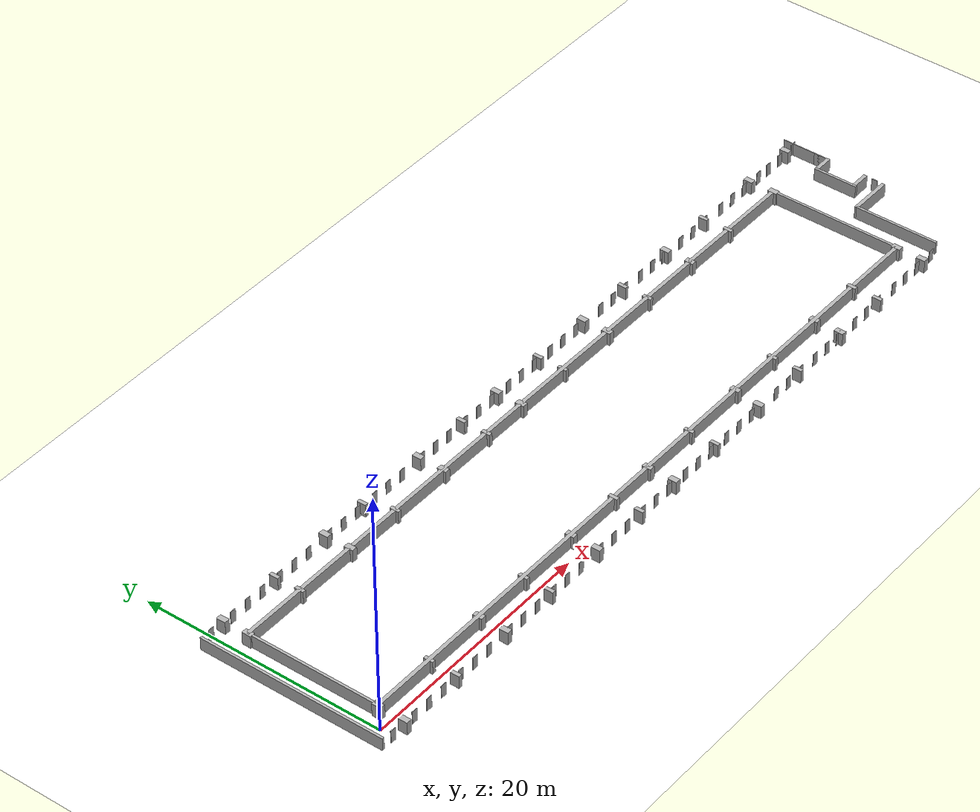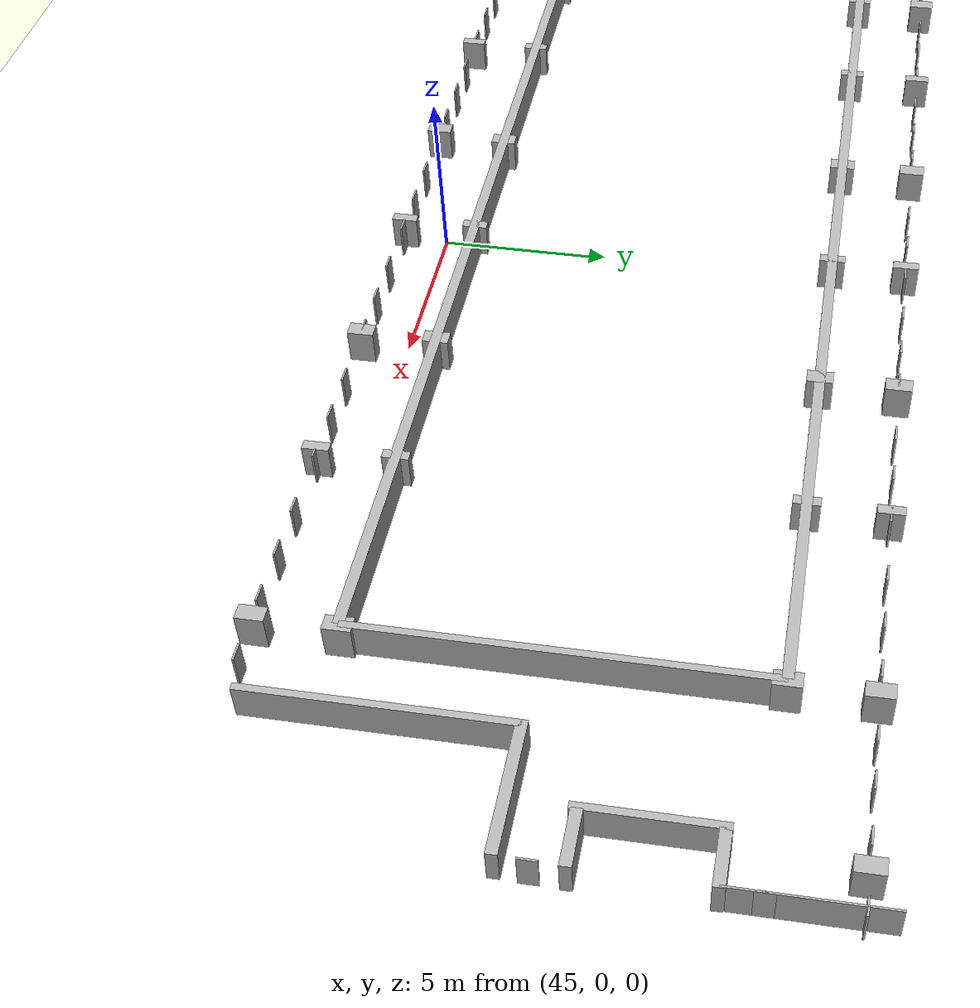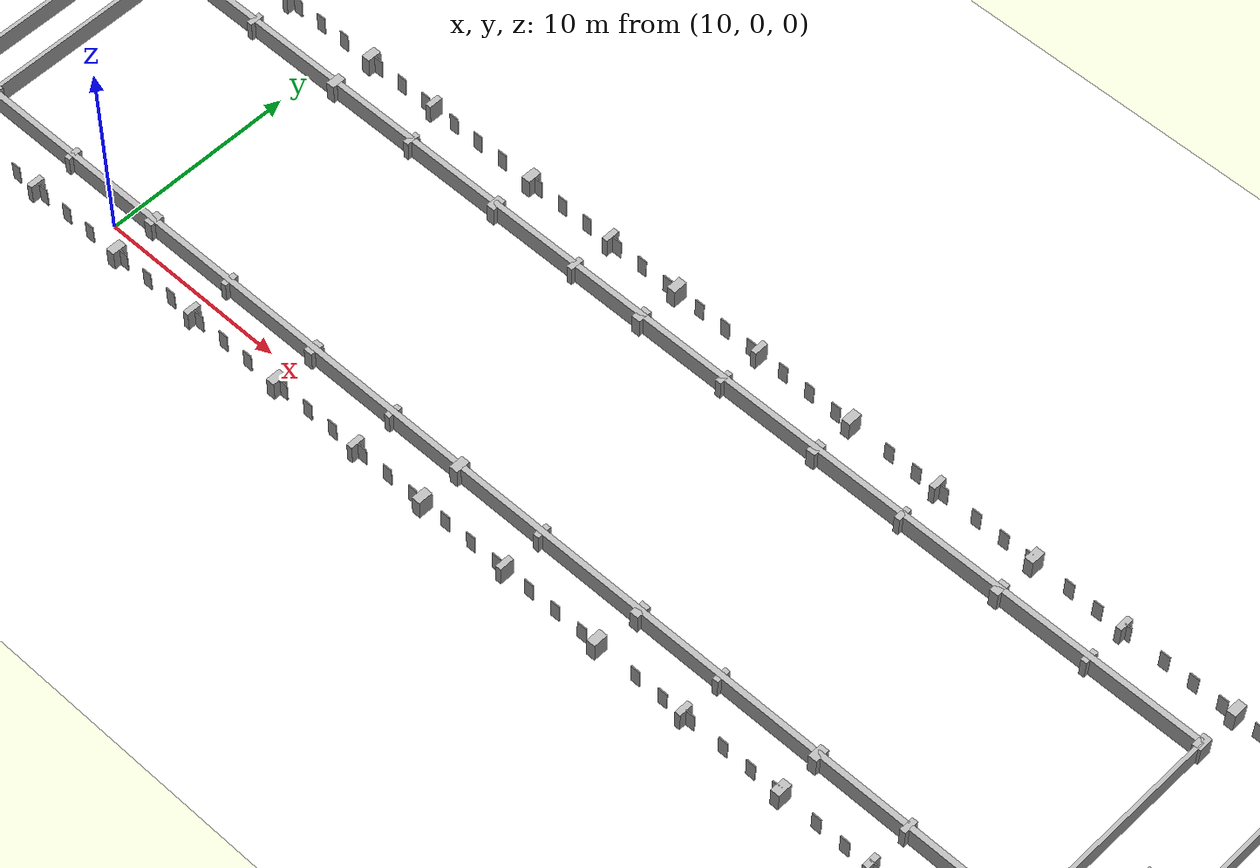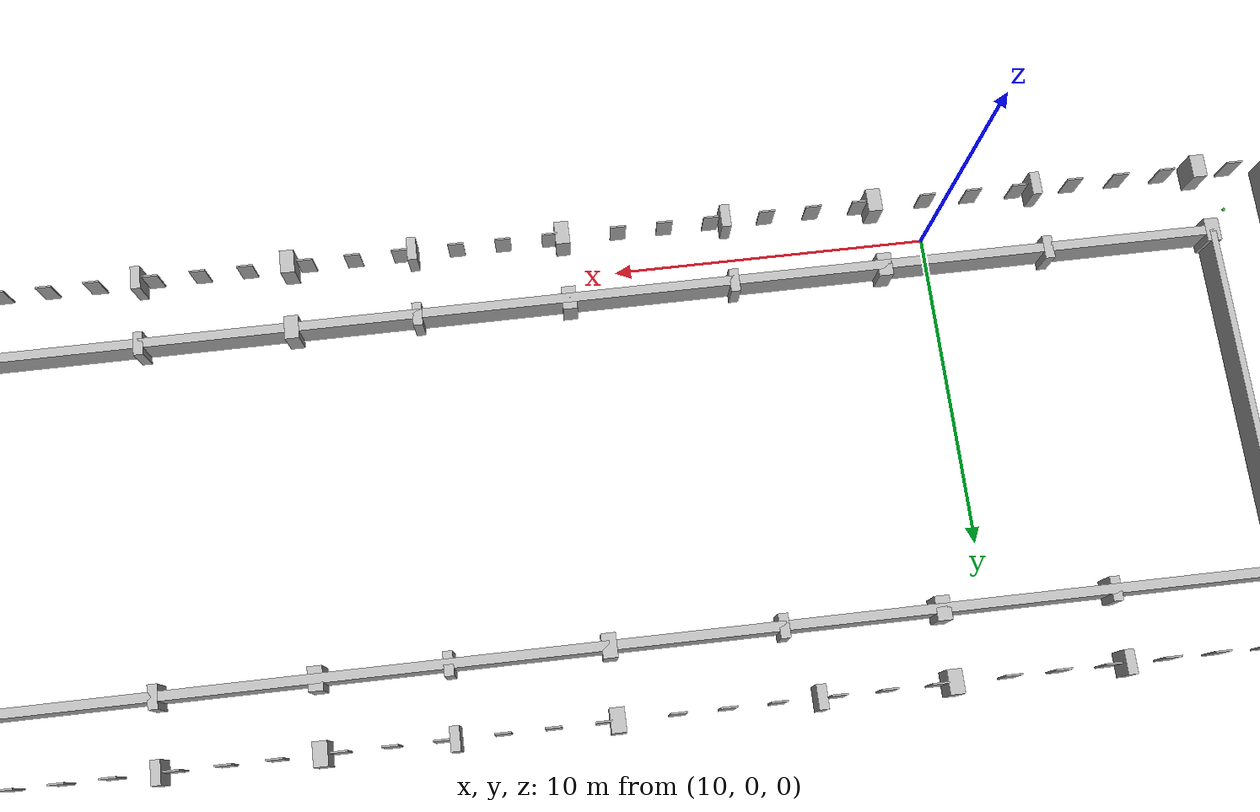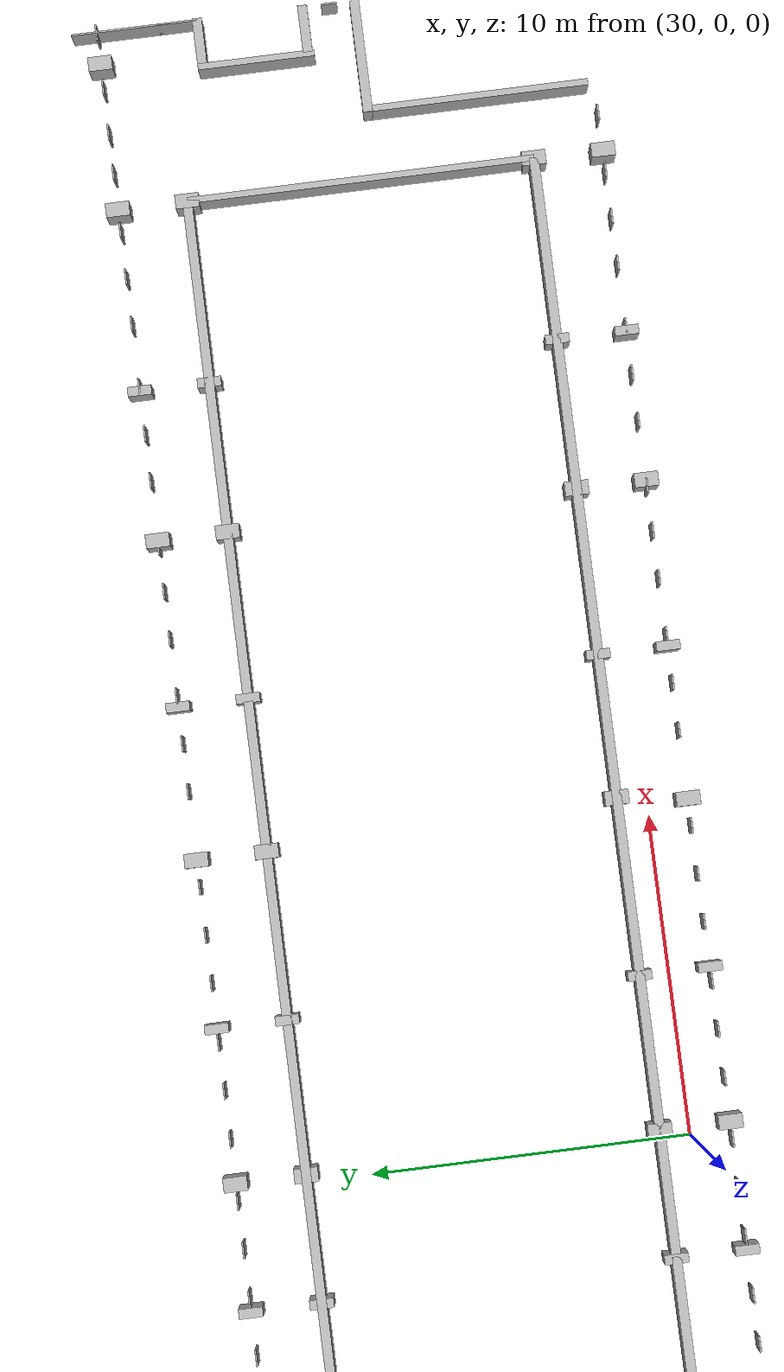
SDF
<?xml version="1.0" ?>
<sdf version="1.7">
  <world name="simple_corridor">

    <!-- Ánh sáng mặt trời -->
    <light name='sun' type='directional'>
      <cast_shadows>false</cast_shadows>
      <pose>0 0 10 0 -0 0</pose>
      <diffuse>0.8 0.8 0.8 1</diffuse>
      <specular>0.2 0.2 0.2 1</specular>
      <attenuation>
        <range>1000</range>
        <constant>0.9</constant>
        <linear>0.01</linear>
        <quadratic>0.001</quadratic>
      </attenuation>
      <direction>-0.5 0.1 -0.9</direction>
    </light>

    <!-- Giao diện người dùng -->
    <gui fullscreen='0'>
      <camera name='user_camera'>
        <pose>-17.1235 6.23259 18.6029 -1e-06 0.831642 -0.454982</pose>
        <view_controller>orbit</view_controller>
        <projection_type>perspective</projection_type>
      </camera>
    </gui>

    <!-- Mặt đất -->
    <model name='ground_plane'>
      <static>true</static>
      <link name='link'>
        <collision name='collision'>
          <geometry>
            <plane>
              <normal>0 0 1</normal>
              <size>500 500</size>
            </plane>
          </geometry>
        </collision>
        <visual name='visual'>
          <geometry>
            <plane>
              <normal>0 0 1</normal>
              <size>500 500</size>
            </plane>
          </geometry>
          <material>
            <ambient>1 1 1 1</ambient>
            <diffuse>1 1 1 1</diffuse>
          </material>
        </visual>
      </link>
    </model>

    <!-- Vật lý -->
    <gravity>0 0 -9.8</gravity>
    <physics type='ode'>
      <max_step_size>0.001</max_step_size>
      <real_time_factor>1</real_time_factor>
      <real_time_update_rate>1000</real_time_update_rate>
    </physics>

    <!-- Cảnh -->
    <scene>
      <ambient>1 1 1 1</ambient>
      <background>1 1 1 1</background>
      <shadows>false</shadows>
    </scene>

    <!-- Hai bức tường -->
    <model name="wall_left">
      <static>true</static>
      <pose>31 12 0 0 0 0</pose>
      <link name="link">
        <collision name="collision">
          <geometry>
            <box>
              <size>60.0 0.3 2.0</size>
            </box>
          </geometry>
        </collision>
        <visual name="visual">
          <geometry>
            <box>
              <size>60.0 0.3 2.0</size>
            </box>
          </geometry>
          <material>
            <diffuse>0.7 0.7 0.7 1</diffuse>
          </material>
        </visual>
      </link>
    </model>

    <model name="wall_right">
      <static>true</static>
      <pose>31 1 0 0 0 0</pose>
      <link name="link">
        <collision name="collision">
          <geometry>
            <box>
              <size>60.0 0.3 2.0</size>
            </box>
          </geometry>
        </collision>
        <visual name="visual">
          <geometry>
            <box>
              <size>60.0 0.3 2.0</size>
            </box>
          </geometry>
          <material>
            <diffuse>0.7 0.7 0.7 1</diffuse>
          </material>
        </visual>
      </link>
      </model>

<model name="wall_start_under">
  <static>true</static>
  <pose>61 6.5 0 0 0 0</pose>  <!-- Bức tường đầu bên phải tại X = 60.2m, Y = 5.5m, Z = 1m -->
  <link name="link">
    <collision name="collision">
      <geometry>
        <box>
          <size>0.2 11 2.0</size>  <!-- Kích thước bức tường: Dài 60m, Rộng 0.2m, Cao 2m -->
        </box>
      </geometry>
    </collision>
    <visual name="visual">
      <geometry>
        <box>
          <size>0.2 11 2.0</size>  <!-- Kích thước bức tường: Dài 60m, Rộng 0.2m, Cao 2m -->
        </box>
      </geometry>
      <material>
        <diffuse>0.7 0.7 0.7 1</diffuse>  <!-- Màu xám cho bức tường -->
      </material>
    </visual>
  </link>
</model>

<model name="wall_start_on">
  <static>true</static>
  <pose>1 6.5 0 0 0 0</pose>
  <link name="link">
    <collision name="collision">
      <geometry>
        <box>
          <size>0.2 11 2.0</size>
        </box>
      </geometry>
    </collision>
    <visual name="visual">
      <geometry>
        <box>
          <size>0.2 11 2.0</size>
        </box>
      </geometry>
      <material>
        <diffuse>0.7 0.7 0.7 1</diffuse>  <!-- Màu xám cho bức tường -->
      </material>
    </visual>
  </link>
</model>

<!-- column left -->
<model name="column_large_left_1">
  <static>true</static>
  <pose>1 12 0 0 0 0</pose>  <!-- Cột lớn tại X = 0, Y = 5.5m, Z = 1m -->
  <link name="link">
    <collision name="collision">
      <geometry>
        <box>
          <size>0.45 0.75 2.0</size>  <!-- Kích thước cột lớn: Dài 0.75m, Rộng 0.2m, Cao 0.2m -->
        </box>
      </geometry>
    </collision>
    <visual name="visual">
      <geometry>
        <box>
          <size>0.45 0.75 2.0</size>  <!-- Kích thước cột lớn: Dài 0.75m, Rộng 0.2m, Cao 0.2m -->
        </box>
      </geometry>
      <material>
        <diffuse>0.7 0.7 0.7 1</diffuse>  <!-- Màu xám cho cột lớn -->
      </material>
    </visual>
  </link>
</model>

<model name="column_small_left_2">
  <static>true</static>
  <pose>6.3 12 0 0 0 0</pose>  <!-- Cột nhỏ tại X = 4.2m, Y = 5.5m, Z = 1m -->
  <link name="link">
    <collision name="collision">
      <geometry>
        <box>
          <size>0.3 0.75 2.0</size>  <!-- Kích thước cột nhỏ: Dài 0.3m, Rộng 0.2m, Cao 0.2m -->
        </box>
      </geometry>
    </collision>
    <visual name="visual">
      <geometry>
        <box>
          <size>0.3 0.75 2.0</size>  <!-- Kích thước cột nhỏ: Dài 0.3m, Rộng 0.2m, Cao 0.2m -->
        </box>
      </geometry>
      <material>
        <diffuse>0.7 0.7 0.7 1</diffuse>  <!-- Màu xám cho cột nhỏ -->
      </material>
    </visual>
  </link>
</model>

<model name="column_large_left_3">
  <static>true</static>
  <pose>11.55 12 0 0 0 0</pose>  <!-- Cột lớn tại X = 0, Y = 5.5m, Z = 1m -->
  <link name="link">
    <collision name="collision">
      <geometry>
        <box>
          <size>0.45 0.75 2.0</size>  <!-- Kích thước cột lớn: Dài 0.75m, Rộng 0.2m, Cao 0.2m -->
        </box>
      </geometry>
    </collision>
    <visual name="visual">
      <geometry>
        <box>
          <size>0.45 0.75 2.0</size>  <!-- Kích thước cột lớn: Dài 0.75m, Rộng 0.2m, Cao 0.2m -->
        </box>
      </geometry>
      <material>
        <diffuse>0.7 0.7 0.7 1</diffuse>  <!-- Màu xám cho cột lớn -->
      </material>
    </visual>
  </link>
</model>

<model name="column_small_left_4">
  <static>true</static>
  <pose>16.35 12 0 0 0 0</pose>  <!-- Cột nhỏ tại X = 4.2m, Y = 5.5m, Z = 1m -->
  <link name="link">
    <collision name="collision">
      <geometry>
        <box>
          <size>0.3 0.75 2.0</size>  <!-- Kích thước cột nhỏ: Dài 0.3m, Rộng 0.2m, Cao 0.2m -->
        </box>
      </geometry>
    </collision>
    <visual name="visual">
      <geometry>
        <box>
          <size>0.3 0.75 2.0</size>  <!-- Kích thước cột nhỏ: Dài 0.3m, Rộng 0.2m, Cao 0.2m -->
        </box>
      </geometry>
      <material>
        <diffuse>0.7 0.7 0.7 1</diffuse>  <!-- Màu xám cho cột nhỏ -->
      </material>
    </visual>
  </link>
</model>

<model name="column_large_left_5">
  <static>true</static>
  <pose>21.6 12 0 0 0 0</pose>  <!-- Cột lớn tại X = 0, Y = 5.5m, Z = 1m -->
  <link name="link">
    <collision name="collision">
      <geometry>
        <box>
          <size>0.45 0.75 2.0</size>  <!-- Kích thước cột lớn: Dài 0.75m, Rộng 0.2m, Cao 0.2m -->
        </box>
      </geometry>
    </collision>
    <visual name="visual">
      <geometry>
        <box>
          <size>0.45 0.75 2.0</size>  <!-- Kích thước cột lớn: Dài 0.75m, Rộng 0.2m, Cao 0.2m -->
        </box>
      </geometry>
      <material>
        <diffuse>0.7 0.7 0.7 1</diffuse>  <!-- Màu xám cho cột lớn -->
      </material>
    </visual>
  </link>
</model>

<model name="column_small_left_6">
  <static>true</static>
  <pose>26.4 12 0 0 0 0</pose>  <!-- Cột nhỏ tại X = 4.2m, Y = 5.5m, Z = 1m -->
  <link name="link">
    <collision name="collision">
      <geometry>
        <box>
          <size>0.3 0.75 2.0</size>  <!-- Kích thước cột nhỏ: Dài 0.3m, Rộng 0.2m, Cao 0.2m -->
        </box>
      </geometry>_right
    </collision>
    <visual name="visual">
      <geometry>
        <box>
          <size>0.3 0.75 2.0</size>  <!-- Kích thước cột nhỏ: Dài 0.3m, Rộng 0.2m, Cao 0.2m -->
        </box>
      </geometry>
      <material>
        <diffuse>0.7 0.7 0.7 1</diffuse>  <!-- Màu xám cho cột nhỏ -->
      </material>
    </visual>
  </link>
</model>

<model name="column_large_left_7">
  <static>true</static>
  <pose>30.35 12 0 0 0 0</pose>  <!-- Cột lớn tại X = 0, Y = 5.5m, Z = 1m -->
  <link name="link">
    <collision name="collision">
      <geometry>
        <box>
          <size>0.45 0.75 2.0</size>  <!-- Kích thước cột lớn: Dài 0.75m, Rộng 0.2m, Cao 0.2m -->
        </box>
      </geometry>
    </collision>
    <visual name="visual">
      <geometry>
        <box>
          <size>0.45 0.75 2.0</size>  <!-- Kích thước cột lớn: Dài 0.75m, Rộng 0.2m, Cao 0.2m -->
        </box>
      </geometry>
      <material>
        <diffuse>0.7 0.7 0.7 1</diffuse>  <!-- Màu xám cho cột lớn -->
      </material>
    </visual>
  </link>
</model>

<model name="column_small_left_8">
  <static>true</static>
  <pose>35.15 12 0 0 0 0</pose>  <!-- Cột nhỏ tại X = 4.2m, Y = 5.5m, Z = 1m -->
  <link name="link">
    <collision name="collision">
      <geometry>
        <box>
          <size>0.3 0.75 2.0</size>  <!-- Kích thước cột nhỏ: Dài 0.3m, Rộng 0.2m, Cao 0.2m -->
        </box>
      </geometry>
    </collision>
    <visual name="visual">
      <geometry>
        <box>
          <size>0.3 0.75 2.0</size>  <!-- Kích thước cột nhỏ: Dài 0.3m, Rộng 0.2m, Cao 0.2m -->
        </box>
      </geometry>
      <material>
        <diffuse>0.7 0.7 0.7 1</diffuse>  <!-- Màu xám cho cột nhỏ -->
      </material>
    </visual>
  </link>
</model>

<model name="column_large_left_9">
  <static>true</static>
  <pose>40.4 12 0 0 0 0</pose>  <!-- Cột lớn tại X = 0, Y = 5.5m, Z = 1m -->
  <link name="link">
    <collision name="collision">
      <geometry>
        <box>
          <size>0.45 0.75 2.0</size>  <!-- Kích thước cột lớn: Dài 0.75m, Rộng 0.2m, Cao 0.2m -->
        </box>
      </geometry>
    </collision>
    <visual name="visual">
      <geometry>
        <box>
          <size>0.45 0.75 2.0</size>  <!-- Kích thước cột lớn: Dài 0.75m, Rộng 0.2m, Cao 0.2m -->
        </box>
      </geometry>
      <material>
        <diffuse>0.7 0.7 0.7 1</diffuse>  <!-- Màu xám cho cột lớn -->
      </material>
    </visual>
  </link>
</model>

<model name="column_small_left_10">
  <static>true</static>
  <pose>45.2 12 0 0 0 0</pose>  <!-- Cột nhỏ tại X = 4.2m, Y = 5.5m, Z = 1m -->
  <link name="link">
    <collision name="collision">
      <geometry>
        <box>
          <size>0.3 0.75 2.0</size>  <!-- Kích thước cột nhỏ: Dài 0.3m, Rộng 0.2m, Cao 0.2m -->
        </box>
      </geometry>
    </collision>
    <visual name="visual">
      <geometry>
        <box>
          <size>0.3 0.75 2.0</size>  <!-- Kích thước cột nhỏ: Dài 0.3m, Rộng 0.2m, Cao 0.2m -->
        </box>
      </geometry>
      <material>
        <diffuse>0.7 0.7 0.7 1</diffuse>  <!-- Màu xám cho cột nhỏ -->
      </material>
    </visual>
  </link>
</model>

<model name="column_large_left_11">
  <static>true</static>
  <pose>50.45 12 0 0 0 0</pose>  <!-- Cột lớn tại X = 0, Y = 5.5m, Z = 1m -->
  <link name="link">
    <collision name="collision">
      <geometry>
        <box>
          <size>0.45 0.75 2.0</size>  <!-- Kích thước cột lớn: Dài 0.75m, Rộng 0.2m, Cao 0.2m -->
        </box>
      </geometry>
    </collision>
    <visual name="visual">
      <geometry>
        <box>
          <size>0.45 0.75 2.0</size>  <!-- Kích thước cột lớn: Dài 0.75m, Rộng 0.2m, Cao 0.2m -->
        </box>
      </geometry>
      <material>
        <diffuse>0.7 0.7 0.7 1</diffuse>  <!-- Màu xám cho cột lớn -->
      </material>
    </visual>
  </link>
</model>

<model name="column_small_left_12">
  <static>true</static>
  <pose>55.2 12 0 0 0 0</pose>  <!-- Cột nhỏ tại X = 4.2m, Y = 5.5m, Z = 1m -->
  <link name="link">
    <collision name="collision">
      <geometry>
        <box>
          <size>0.3 0.75 2.0</size>  <!-- Kích thước cột nhỏ: Dài 0.3m, Rộng 0.2m, Cao 0.2m -->
        </box>
      </geometry>
    </collision>
    <visual name="visual">
      <geometry>
        <box>
          <size>0.3 0.75 2.0</size>  <!-- Kích thước cột nhỏ: Dài 0.3m, Rộng 0.2m, Cao 0.2m -->
        </box>
      </geometry>
      <material>
        <diffuse>0.7 0.7 0.7 1</diffuse>  <!-- Màu xám cho cột nhỏ -->
      </material>
    </visual>
  </link>
</model>

<model name="column_large_left_13">
  <static>true</static>
  <pose>61 12 0 0 0 0</pose>  <!-- Cột lớn tại X = 0, Y = 5.5m, Z = 1m -->
  <link name="link">
    <collision name="collision">
      <geometry>
        <box>
          <size>0.45 0.75 2.0</size>  <!-- Kích thước cột lớn: Dài 0.75m, Rộng 0.2m, Cao 0.2m -->
        </box>
      </geometry>
    </collision>
    <visual name="visual">
      <geometry>
        <box>
          <size>0.45 0.75 2.0</size>  <!-- Kích thước cột lớn: Dài 0.75m, Rộng 0.2m, Cao 0.2m -->
        </box>
      </geometry>
      <material>
        <diffuse>0.7 0.7 0.7 1</diffuse>  <!-- Màu xám cho cột lớn -->
      </material>
    </visual>
  </link>
</model>

<!-- column right  -->
<model name="column_large_right_1">
  <static>true</static>
  <pose>1 1 0 0 0 0</pose>  <!-- Cột lớn tại X = 0, Y = 5.5m, Z = 1m -->
  <link name="link">
    <collision name="collision">
      <geometry>
        <box>
          <size>0.45 0.75 2.0</size>  <!-- Kích thước cột lớn: Dài 0.75m, Rộng 0.2m, Cao 0.2m -->
        </box>
      </geometry>
    </collision>
    <visual name="visual">
      <geometry>
        <box>
          <size>0.45 0.75 2.0</size>  <!-- Kích thước cột lớn: Dài 0.75m, Rộng 0.2m, Cao 0.2m -->
        </box>
      </geometry>
      <material>
        <diffuse>0.7 0.7 0.7 1</diffuse>  <!-- Màu xám cho cột lớn -->
      </material>
    </visual>
  </link>
</model>

<model name="column_small_right_2">
  <static>true</static>
  <pose>6.3 1 0 0 0 0</pose>  <!-- Cột nhỏ tại X = 4.2m, Y = 5.5m, Z = 1m -->
  <link name="link">
    <collision name="collision">
      <geometry>
        <box>
          <size>0.3 0.75 2.0</size>  <!-- Kích thước cột nhỏ: Dài 0.3m, Rộng 0.2m, Cao 0.2m -->
        </box>
      </geometry>
    </collision>
    <visual name="visual">
      <geometry>
        <box>
          <size>0.3 0.75 2.0</size>  <!-- Kích thước cột nhỏ: Dài 0.3m, Rộng 0.2m, Cao 0.2m -->
        </box>
      </geometry>
      <material>
        <diffuse>0.7 0.7 0.7 1</diffuse>  <!-- Màu xám cho cột nhỏ -->
      </material>
    </visual>
  </link>
</model>

<model name="column_large_right_3">
  <static>true</static>
  <pose>11.55 1 0 0 0 0</pose>  <!-- Cột lớn tại X = 0, Y = 5.5m, Z = 1m -->
  <link name="link">
    <collision name="collision">
      <geometry>
        <box>
          <size>0.45 0.75 2.0</size>  <!-- Kích thước cột lớn: Dài 0.75m, Rộng 0.2m, Cao 0.2m -->
        </box>
      </geometry>
    </collision>
    <visual name="visual">
      <geometry>
        <box>
          <size>0.45 0.75 2.0</size>  <!-- Kích thước cột lớn: Dài 0.75m, Rộng 0.2m, Cao 0.2m -->
        </box>
      </geometry>
      <material>
        <diffuse>0.7 0.7 0.7 1</diffuse>  <!-- Màu xám cho cột lớn -->
      </material>
    </visual>
  </link>
</model>

<model name="column_small_right_4">
  <static>true</static>
  <pose>16.35 1 0 0 0 0</pose>  <!-- Cột nhỏ tại X = 4.2m, Y = 5.5m, Z = 1m -->
  <link name="link">
    <collision name="collision">
      <geometry>
        <box>
          <size>0.3 0.75 2.0</size>  <!-- Kích thước cột nhỏ: Dài 0.3m, Rộng 0.2m, Cao 0.2m -->
        </box>
      </geometry>
    </collision>
    <visual name="visual">
      <geometry>
        <box>
          <size>0.3 0.75 2.0</size>  <!-- Kích thước cột nhỏ: Dài 0.3m, Rộng 0.2m, Cao 0.2m -->
        </box>
      </geometry>
      <material>
        <diffuse>0.7 0.7 0.7 1</diffuse>  <!-- Màu xám cho cột nhỏ -->
      </material>
    </visual>
  </link>
</model>

<model name="column_large_right_5">
  <static>true</static>
  <pose>21.6 1 0 0 0 0</pose>  <!-- Cột lớn tại X = 0, Y = 5.5m, Z = 1m -->
  <link name="link">
    <collision name="collision">
      <geometry>
        <box>
          <size>0.45 0.75 2.0</size>  <!-- Kích thước cột lớn: Dài 0.75m, Rộng 0.2m, Cao 0.2m -->
        </box>
      </geometry>
    </collision>
    <visual name="visual">
      <geometry>
        <box>
          <size>0.45 0.75 2.0</size>  <!-- Kích thước cột lớn: Dài 0.75m, Rộng 0.2m, Cao 0.2m -->
        </box>
      </geometry>
      <material>
        <diffuse>0.7 0.7 0.7 1</diffuse>  <!-- Màu xám cho cột lớn -->
      </material>
    </visual>
  </link>
</model>

<model name="column_small_right_6">
  <static>true</static>
  <pose>26.4 1 0 0 0 0</pose>  <!-- Cột nhỏ tại X = 4.2m, Y = 5.5m, Z = 1m -->
  <link name="link">
    <collision name="collision">
      <geometry>
        <box>
          <size>0.3 0.75 2.0</size>  <!-- Kích thước cột nhỏ: Dài 0.3m, Rộng 0.2m, Cao 0.2m -->
        </box>
      </geometry>
    </collision>
    <visual name="visual">
      <geometry>
        <box>
          <size>0.3 0.75 2.0</size>  <!-- Kích thước cột nhỏ: Dài 0.3m, Rộng 0.2m, Cao 0.2m -->
        </box>
      </geometry>
      <material>
        <diffuse>0.7 0.7 0.7 1</diffuse>  <!-- Màu xám cho cột nhỏ -->
      </material>
    </visual>
  </link>
</model>

<model name="column_large_right_7">
  <static>true</static>
  <pose>30.35 1 0 0 0 0</pose>  <!-- Cột lớn tại X = 0, Y = 5.5m, Z = 1m -->
  <link name="link">
    <collision name="collision">
      <geometry>
        <box>
          <size>0.45 0.75 2.0</size>  <!-- Kích thước cột lớn: Dài 0.75m, Rộng 0.2m, Cao 0.2m -->
        </box>
      </geometry>
    </collision>
    <visual name="visual">
      <geometry>
        <box>
          <size>0.45 0.75 2.0</size>  <!-- Kích thước cột lớn: Dài 0.75m, Rộng 0.2m, Cao 0.2m -->
        </box>
      </geometry>
      <material>
        <diffuse>0.7 0.7 0.7 1</diffuse>  <!-- Màu xám cho cột lớn -->
      </material>
    </visual>
  </link>
</model>

<model name="column_small_right_8">
  <static>true</static>
  <pose>35.15 1 0 0 0 0</pose>  <!-- Cột nhỏ tại X = 4.2m, Y = 5.5m, Z = 1m -->
  <link name="link">
    <collision name="collision">
      <geometry>
        <box>
          <size>0.3 0.75 2.0</size>  <!-- Kích thước cột nhỏ: Dài 0.3m, Rộng 0.2m, Cao 0.2m -->
        </box>
      </geometry>
    </collision>
    <visual name="visual">
      <geometry>
        <box>
          <size>0.3 0.75 2.0</size>  <!-- Kích thước cột nhỏ: Dài 0.3m, Rộng 0.2m, Cao 0.2m -->
        </box>
      </geometry>
      <material>
        <diffuse>0.7 0.7 0.7 1</diffuse>  <!-- Màu xám cho cột nhỏ -->
      </material>
    </visual>
  </link>
</model>

<model name="column_large_right_9">
  <static>true</static>
  <pose>40.7 1 0 0 0 0</pose>  <!-- Cột lớn tại X = 0, Y = 5.5m, Z = 1m -->
  <link name="link">
    <collision name="collision">
      <geometry>
        <box>
          <size>0.45 0.75 2.0</size>  <!-- Kích thước cột lớn: Dài 0.75m, Rộng 0.2m, Cao 0.2m -->
        </box>
      </geometry>
    </collision>
    <visual name="visual">
      <geometry>
        <box>
          <size>0.45 0.75 2.0</size>  <!-- Kích thước cột lớn: Dài 0.75m, Rộng 0.2m, Cao 0.2m -->
        </box>
      </geometry>
      <material>
        <diffuse>0.7 0.7 0.7 1</diffuse>  <!-- Màu xám cho cột lớn -->
      </material>
    </visual>
  </link>
</model>

<model name="column_small_right_10">
  <static>true</static>
  <pose>45.2 1 0 0 0 0</pose>  <!-- Cột nhỏ tại X = 4.2m, Y = 5.5m, Z = 1m -->
  <link name="link">
    <collision name="collision">
      <geometry>
        <box>
          <size>0.3 0.75 2.0</size>  <!-- Kích thước cột nhỏ: Dài 0.3m, Rộng 0.2m, Cao 0.2m -->
        </box>
      </geometry>
    </collision>
    <visual name="visual">
      <geometry>
        <box>
          <size>0.3 0.75 2.0</size>  <!-- Kích thước cột nhỏ: Dài 0.3m, Rộng 0.2m, Cao 0.2m -->
        </box>
      </geometry>
      <material>
        <diffuse>0.7 0.7 0.7 1</diffuse>  <!-- Màu xám cho cột nhỏ -->
      </material>
    </visual>
  </link>
</model>

<model name="column_large_right_11">
  <static>true</static>
  <pose>50.45 1 0 0 0 0</pose>  <!-- Cột lớn tại X = 0, Y = 5.5m, Z = 1m -->
  <link name="link">
    <collision name="collision">
      <geometry>
        <box>
          <size>0.45 0.75 2.0</size>  <!-- Kích thước cột lớn: Dài 0.75m, Rộng 0.2m, Cao 0.2m -->
        </box>
      </geometry>
    </collision>
    <visual name="visual">
      <geometry>
        <box>
          <size>0.45 0.75 2.0</size>  <!-- Kích thước cột lớn: Dài 0.75m, Rộng 0.2m, Cao 0.2m -->
        </box>
      </geometry>
      <material>
        <diffuse>0.7 0.7 0.7 1</diffuse>  <!-- Màu xám cho cột lớn -->
      </material>
    </visual>
  </link>
</model>

<model name="column_small_right_12">
  <static>true</static>
  <pose>55.2 1 0 0 0 0</pose>  <!-- Cột nhỏ tại X = 4.2m, Y = 5.5m, Z = 1m -->
  <link name="link">
    <collision name="collision">
      <geometry>
        <box>
          <size>0.3 0.75 2.0</size>  <!-- Kích thước cột nhỏ: Dài 0.3m, Rộng 0.2m, Cao 0.2m -->
        </box>
      </geometry>
    </collision>
    <visual name="visual">
      <geometry>
        <box>
          <size>0.3 0.75 2.0</size>  <!-- Kích thước cột nhỏ: Dài 0.3m, Rộng 0.2m, Cao 0.2m -->
        </box>
      </geometry>
      <material>
        <diffuse>0.7 0.7 0.7 1</diffuse>  <!-- Màu xám cho cột nhỏ -->
      </material>
    </visual>
  </link>
</model>

<model name="column_large_right_13">
  <static>true</static>
  <pose>61 1 0 0 0 0</pose>  <!-- Cột lớn tại X = 0, Y = 5.5m, Z = 1m -->
  <link name="link">
    <collision name="collision">
      <geometry>
        <box>
          <size>0.45 0.75 2.0</size>  <!-- Kích thước cột lớn: Dài 0.75m, Rộng 0.2m, Cao 0.2m -->
        </box>
      </geometry>
    </collision>
    <visual name="visual">
      <geometry>
        <box>
          <size>0.45 0.75 2.0</size>  <!-- Kích thước cột lớn: Dài 0.75m, Rộng 0.2m, Cao 0.2m -->
        </box>
      </geometry>
      <material>
        <diffuse>0.7 0.7 0.7 1</diffuse>  <!-- Màu xám cho cột lớn -->
      </material>
    </visual>
  </link>
</model>

<!-- banister left-->
<model name="ban_large_left_1">
  <static>true</static>
  <pose>1 14.2 0 0 0 0</pose>  <!-- Cột lớn tại X = 0, Y = 5.5m, Z = 1m -->
  <link name="link">
    <collision name="collision">
      <geometry>
        <box>
          <size>0.45 0.75 2.0</size>  <!-- Kích thước cột lớn: Dài 0.75m, Rộng 0.2m, Cao 0.2m -->
        </box>
      </geometry>
    </collision>
    <visual name="visual">
      <geometry>
        <box>
          <size>0.45 0.75 2.0</size>  <!-- Kích thước cột lớn: Dài 0.75m, Rộng 0.2m, Cao 0.2m -->
        </box>
      </geometry>
      <material>
        <diffuse>0.7 0.7 0.7 1</diffuse>  <!-- Màu xám cho cột lớn -->
      </material>
    </visual>
  </link>
</model>

<model name="ban_small_left_2">
  <static>true</static>
  <pose>6.3 14.2 0 0 0 0</pose>  <!-- Cột nhỏ tại X = 4.2m, Y = 5.5m, Z = 1m -->
  <link name="link">
    <collision name="collision">
      <geometry>
        <box>
          <size>0.3 0.75 2.0</size>  <!-- Kích thước cột nhỏ: Dài 0.3m, Rộng 0.2m, Cao 0.2m -->
        </box>
      </geometry>
    </collision>
    <visual name="visual">
      <geometry>
        <box>
          <size>0.3 0.75 2.0</size>  <!-- Kích thước cột nhỏ: Dài 0.3m, Rộng 0.2m, Cao 0.2m -->
        </box>
      </geometry>
      <material>
        <diffuse>0.7 0.7 0.7 1</diffuse>  <!-- Màu xám cho cột nhỏ -->
      </material>
    </visual>
  </link>
</model>

<model name="ban_large_left_3">
  <static>true</static>
  <pose>11.55 14.2 0 0 0 0</pose>  <!-- Cột lớn tại X = 0, Y = 5.5m, Z = 1m -->
  <link name="link">
    <collision name="collision">
      <geometry>
        <box>
          <size>0.45 0.75 2.0</size>  <!-- Kích thước cột lớn: Dài 0.75m, Rộng 0.2m, Cao 0.2m -->
        </box>
      </geometry>
    </collision>
    <visual name="visual">
      <geometry>
        <box>
          <size>0.45 0.75 2.0</size>  <!-- Kích thước cột lớn: Dài 0.75m, Rộng 0.2m, Cao 0.2m -->
        </box>
      </geometry>
      <material>
        <diffuse>0.7 0.7 0.7 1</diffuse>  <!-- Màu xám cho cột lớn -->
      </material>
    </visual>
  </link>
</model>

<model name="ban_small_left_4">
  <static>true</static>
  <pose>15.53 14.2 0 0 0 0</pose>  <!-- Cột nhỏ tại X = 4.2m, Y = 5.5m, Z = 1m -->
  <link name="link">
    <collision name="collision">
      <geometry>
        <box>
          <size>0.3 0.75 2.0</size>  <!-- Kích thước cột nhỏ: Dài 0.3m, Rộng 0.2m, Cao 0.2m -->
        </box>
      </geometry>
    </collision>
    <visual name="visual">
      <geometry>
        <box>
          <size>0.3 0.75 2.0</size>  <!-- Kích thước cột nhỏ: Dài 0.3m, Rộng 0.2m, Cao 0.2m -->
        </box>
      </geometry>
      <material>
        <diffuse>0.7 0.7 0.7 1</diffuse>  <!-- Màu xám cho cột nhỏ -->
      </material>
    </visual>
  </link>
</model>

<model name="ban_large_left_5">
  <static>true</static>
  <pose>21.6 14.2 0 0 0 0</pose>  <!-- Cột lớn tại X = 0, Y = 5.5m, Z = 1m -->
  <link name="link">
    <collision name="collision">
      <geometry>
        <box>
          <size>0.45 0.75 2.0</size>  <!-- Kích thước cột lớn: Dài 0.75m, Rộng 0.2m, Cao 0.2m -->
        </box>
      </geometry>
    </collision>
    <visual name="visual">
      <geometry>
        <box>
          <size>0.45 0.75 2.0</size>  <!-- Kích thước cột lớn: Dài 0.75m, Rộng 0.2m, Cao 0.2m -->
        </box>
      </geometry>
      <material>
        <diffuse>0.7 0.7 0.7 1</diffuse>  <!-- Màu xám cho cột lớn -->
      </material>
    </visual>
  </link>
</model>

<model name="ban_small_left_6">
  <static>true</static>
  <pose>26.4 14.2 0 0 0 0</pose>  <!-- Cột nhỏ tại X = 4.2m, Y = 5.5m, Z = 1m -->
  <link name="link">
    <collision name="collision">
      <geometry>
        <box>
          <size>0.3 0.75 2.0</size>  <!-- Kích thước cột nhỏ: Dài 0.3m, Rộng 0.2m, Cao 0.2m -->
        </box>
      </geometry>
    </collision>
    <visual name="visual">
      <geometry>
        <box>
          <size>0.3 0.75 2.0</size>  <!-- Kích thước cột nhỏ: Dài 0.3m, Rộng 0.2m, Cao 0.2m -->
        </box>
      </geometry>
      <material>
        <diffuse>0.7 0.7 0.7 1</diffuse>  <!-- Màu xám cho cột nhỏ -->
      </material>
    </visual>
  </link>
</model>

<model name="ban_large_left_7">
  <static>true</static>
  <pose>30.35 14.2 0 0 0 0</pose>  <!-- Cột lớn tại X = 0, Y = 5.5m, Z = 1m -->
  <link name="link">
    <collision name="collision">
      <geometry>
        <box>
          <size>0.45 0.75 2.0</size>  <!-- Kích thước cột lớn: Dài 0.75m, Rộng 0.2m, Cao 0.2m -->
        </box>
      </geometry>
    </collision>
    <visual name="visual">
      <geometry>
        <box>
          <size>0.45 0.75 2.0</size>  <!-- Kích thước cột lớn: Dài 0.75m, Rộng 0.2m, Cao 0.2m -->
        </box>
      </geometry>
      <material>
        <diffuse>0.7 0.7 0.7 1</diffuse>  <!-- Màu xám cho cột lớn -->
      </material>
    </visual>
  </link>
</model>

<model name="ban_small_left_8">
  <static>true</static>
  <pose>35.15 14.2 0 0 0 0</pose>  <!-- Cột nhỏ tại X = 4.2m, Y = 5.5m, Z = 1m -->
  <link name="link">
    <collision name="collision">
      <geometry>
        <box>
          <size>0.3 0.75 2.0</size>  <!-- Kích thước cột nhỏ: Dài 0.3m, Rộng 0.2m, Cao 0.2m -->
        </box>
      </geometry>
    </collision>
    <visual name="visual">
      <geometry>
        <box>
          <size>0.3 0.75 2.0</size>  <!-- Kích thước cột nhỏ: Dài 0.3m, Rộng 0.2m, Cao 0.2m -->
        </box>
      </geometry>
      <material>
        <diffuse>0.7 0.7 0.7 1</diffuse>  <!-- Màu xám cho cột nhỏ -->
      </material>
    </visual>
  </link>
</model>

<model name="ban_large_left_9">
  <static>true</static>
  <pose>40.4 14.2 0 0 0 0</pose>  <!-- Cột lớn tại X = 0, Y = 5.5m, Z = 1m -->
  <link name="link">
    <collision name="collision">
      <geometry>
        <box>
          <size>0.45 0.75 2.0</size>  <!-- Kích thước cột lớn: Dài 0.75m, Rộng 0.2m, Cao 0.2m -->
        </box>
      </geometry>
    </collision>
    <visual name="visual">
      <geometry>
        <box>
          <size>0.45 0.75 2.0</size>  <!-- Kích thước cột lớn: Dài 0.75m, Rộng 0.2m, Cao 0.2m -->
        </box>
      </geometry>
      <material>
        <diffuse>0.7 0.7 0.7 1</diffuse>  <!-- Màu xám cho cột lớn -->
      </material>
    </visual>
  </link>
</model>

<model name="ban_small_left_10">
  <static>true</static>
  <pose>45.2 14.2 0 0 0 0</pose>  <!-- Cột nhỏ tại X = 4.2m, Y = 5.5m, Z = 1m -->
  <link name="link">
    <collision name="collision">
      <geometry>
        <box>
          <size>0.3 0.75 2.0</size>  <!-- Kích thước cột nhỏ: Dài 0.3m, Rộng 0.2m, Cao 0.2m -->
        </box>
      </geometry>
    </collision>
    <visual name="visual">
      <geometry>
        <box>
          <size>0.3 0.75 2.0</size>  <!-- Kích thước cột nhỏ: Dài 0.3m, Rộng 0.2m, Cao 0.2m -->
        </box>
      </geometry>
      <material>
        <diffuse>0.7 0.7 0.7 1</diffuse>  <!-- Màu xám cho cột nhỏ -->
      </material>
    </visual>
  </link>
</model>

<model name="ban_large_left_11">
  <static>true</static>
  <pose>50.45 14.2 0 0 0 0</pose>  <!-- Cột lớn tại X = 0, Y = 5.5m, Z = 1m -->
  <link name="link">
    <collision name="collision">
      <geometry>
        <box>
          <size>0.45 0.75 2.0</size>  <!-- Kích thước cột lớn: Dài 0.75m, Rộng 0.2m, Cao 0.2m -->
        </box>
      </geometry>
    </collision>
    <visual name="visual">
      <geometry>
        <box>
          <size>0.45 0.75 2.0</size>  <!-- Kích thước cột lớn: Dài 0.75m, Rộng 0.2m, Cao 0.2m -->
        </box>
      </geometry>
      <material>
        <diffuse>0.7 0.7 0.7 1</diffuse>  <!-- Màu xám cho cột lớn -->
      </material>
    </visual>
  </link>
</model>

<model name="ban_small_left_12">
  <static>true</static>
  <pose>55.2 14.2 0 0 0 0</pose>  <!-- Cột nhỏ tại X = 4.2m, Y = 5.5m, Z = 1m -->
  <link name="link">
    <collision name="collision">
      <geometry>
        <box>
          <size>0.3 0.75 2.0</size>  <!-- Kích thước cột nhỏ: Dài 0.3m, Rộng 0.2m, Cao 0.2m -->
        </box>
      </geometry>
    </collision>
    <visual name="visual">
      <geometry>
        <box>
          <size>0.3 0.75 2.0</size>  <!-- Kích thước cột nhỏ: Dài 0.3m, Rộng 0.2m, Cao 0.2m -->
        </box>
      </geometry>
      <material>
        <diffuse>0.7 0.7 0.7 1</diffuse>  <!-- Màu xám cho cột nhỏ -->
      </material>
    </visual>
  </link>
</model>

<model name="ban_large_left_13">
  <static>true</static>
  <pose>61 14.2 0 0 0 0</pose>  <!-- Cột lớn tại X = 0, Y = 5.5m, Z = 1m -->
  <link name="link">
    <collision name="collision">
      <geometry>
        <box>
          <size>0.45 0.75 2.0</size>  <!-- Kích thước cột lớn: Dài 0.75m, Rộng 0.2m, Cao 0.2m -->
        </box>
      </geometry>
    </collision>
    <visual name="visual">
      <geometry>
        <box>
          <size>0.45 0.75 2.0</size>  <!-- Kích thước cột lớn: Dài 0.75m, Rộng 0.2m, Cao 0.2m -->
        </box>
      </geometry>
      <material>
        <diffuse>0.7 0.7 0.7 1</diffuse>  <!-- Màu xám cho cột lớn -->
      </material>
    </visual>
  </link>
</model>

<!-- banister right -->
<model name="ban_large_right_1">
  <static>true</static>
  <pose>1 -1.2 0 0 0 0</pose>  <!-- Cột lớn tại X = 0, Y = 5.5m, Z = 1m -->
  <link name="link">
    <collision name="collision">
      <geometry>
        <box>
          <size>0.45 0.75 2.0</size>  <!-- Kích thước cột lớn: Dài 0.75m, Rộng 0.2m, Cao 0.2m -->
        </box>
      </geometry>
    </collision>
    <visual name="visual">
      <geometry>
        <box>
          <size>0.45 0.75 2.0</size>  <!-- Kích thước cột lớn: Dài 0.75m, Rộng 0.2m, Cao 0.2m -->
        </box>
      </geometry>
      <material>
        <diffuse>0.7 0.7 0.7 1</diffuse>  <!-- Màu xám cho cột lớn -->
      </material>
    </visual>
  </link>
</model>

<model name="ban_small_right_2">
  <static>true</static>
  <pose>6.3 -1.2 0 0 0 0</pose>  <!-- Cột nhỏ tại X = 4.2m, Y = 5.5m, Z = 1m -->
  <link name="link">
    <collision name="collision">
      <geometry>
        <box>
          <size>0.3 0.75 2.0</size>  <!-- Kích thước cột nhỏ: Dài 0.3m, Rộng 0.2m, Cao 0.2m -->
        </box>
      </geometry>
    </collision>
    <visual name="visual">
      <geometry>
        <box>
          <size>0.3 0.75 2.0</size>  <!-- Kích thước cột nhỏ: Dài 0.3m, Rộng 0.2m, Cao 0.2m -->
        </box>
      </geometry>
      <material>
        <diffuse>0.7 0.7 0.7 1</diffuse>  <!-- Màu xám cho cột nhỏ -->
      </material>
    </visual>
  </link>
</model>

<model name="ban_large_right_3">
  <static>true</static>
  <pose>11.55 -1.2 0 0 0 0</pose>  <!-- Cột lớn tại X = 0, Y = 5.5m, Z = 1m -->
  <link name="link">
    <collision name="collision">
      <geometry>
        <box>
          <size>0.45 0.75 2.0</size>  <!-- Kích thước cột lớn: Dài 0.75m, Rộng 0.2m, Cao 0.2m -->
        </box>
      </geometry>
    </collision>
    <visual name="visual">
      <geometry>
        <box>
          <size>0.45 0.75 2.0</size>  <!-- Kích thước cột lớn: Dài 0.75m, Rộng 0.2m, Cao 0.2m -->
        </box>
      </geometry>
      <material>
        <diffuse>0.7 0.7 0.7 1</diffuse>  <!-- Màu xám cho cột lớn -->
      </material>
    </visual>
  </link>
</model>

<model name="ban_small_right_4">
  <static>true</static>
  <pose>16.35 -1.2 0 0 0 0</pose>  <!-- Cột nhỏ tại X = 4.2m, Y = 5.5m, Z = 1m -->
  <link name="link">
    <collision name="collision">
      <geometry>
        <box>
          <size>0.3 0.75 2.0</size>  <!-- Kích thước cột nhỏ: Dài 0.3m, Rộng 0.2m, Cao 0.2m -->
        </box>
      </geometry>
    </collision>
    <visual name="visual">
      <geometry>
        <box>
          <size>0.3 0.75 2.0</size>  <!-- Kích thước cột nhỏ: Dài 0.3m, Rộng 0.2m, Cao 0.2m -->
        </box>
      </geometry>
      <material>
        <diffuse>0.7 0.7 0.7 1</diffuse>  <!-- Màu xám cho cột nhỏ -->
      </material>
    </visual>
  </link>
</model>

<model name="ban_large_right_5">
  <static>true</static>
  <pose>21.6 -1.2 0 0 0 0</pose>  <!-- Cột lớn tại X = 0, Y = 5.5m, Z = 1m -->
  <link name="link">
    <collision name="collision">
      <geometry>
        <box>
          <size>0.45 0.75 2.0</size>  <!-- Kích thước cột lớn: Dài 0.75m, Rộng 0.2m, Cao 0.2m -->
        </box>
      </geometry>
    </collision>
    <visual name="visual">
      <geometry>
        <box>
          <size>0.45 0.75 2.0</size>  <!-- Kích thước cột lớn: Dài 0.75m, Rộng 0.2m, Cao 0.2m -->
        </box>
      </geometry>
      <material>
        <diffuse>0.7 0.7 0.7 1</diffuse>  <!-- Màu xám cho cột lớn -->
      </material>
    </visual>
  </link>
</model>

<model name="ban_small_right_6">
  <static>true</static>
  <pose>26.4 -1.2 0 0 0 0</pose>  <!-- Cột nhỏ tại X = 4.2m, Y = 5.5m, Z = 1m -->
  <link name="link">
    <collision name="collision">
      <geometry>
        <box>
          <size>0.3 0.75 2.0</size>  <!-- Kích thước cột nhỏ: Dài 0.3m, Rộng 0.2m, Cao 0.2m -->
        </box>
      </geometry>
    </collision>
    <visual name="visual">
      <geometry>
        <box>
          <size>0.3 0.75 2.0</size>  <!-- Kích thước cột nhỏ: Dài 0.3m, Rộng 0.2m, Cao 0.2m -->
        </box>
      </geometry>
      <material>
        <diffuse>0.7 0.7 0.7 1</diffuse>  <!-- Màu xám cho cột nhỏ -->
      </material>
    </visual>
  </link>
</model>

<model name="ban_large_right_7">
  <static>true</static>
  <pose>30.35 -1.2 0 0 0 0</pose>  <!-- Cột lớn tại X = 0, Y = 5.5m, Z = 1m -->
  <link name="link">
    <collision name="collision">
      <geometry>
        <box>
          <size>0.45 0.75 2.0</size>  <!-- Kích thước cột lớn: Dài 0.75m, Rộng 0.2m, Cao 0.2m -->
        </box>
      </geometry>
    </collision>
    <visual name="visual">
      <geometry>
        <box>
          <size>0.45 0.75 2.0</size>  <!-- Kích thước cột lớn: Dài 0.75m, Rộng 0.2m, Cao 0.2m -->
        </box>
      </geometry>
      <material>
        <diffuse>0.7 0.7 0.7 1</diffuse>  <!-- Màu xám cho cột lớn -->
      </material>
    </visual>
  </link>
</model>

<model name="ban_small_right_8">
  <static>true</static>
  <pose>35.15 -1.2 0 0 0 0</pose>  <!-- Cột nhỏ tại X = 4.2m, Y = 5.5m, Z = 1m -->
  <link name="link">
    <collision name="collision">
      <geometry>
        <box>
          <size>0.3 0.75 2.0</size>  <!-- Kích thước cột nhỏ: Dài 0.3m, Rộng 0.2m, Cao 0.2m -->
        </box>
      </geometry>
    </collision>
    <visual name="visual">
      <geometry>
        <box>
          <size>0.3 0.75 2.0</size>  <!-- Kích thước cột nhỏ: Dài 0.3m, Rộng 0.2m, Cao 0.2m -->
        </box>
      </geometry>
      <material>
        <diffuse>0.7 0.7 0.7 1</diffuse>  <!-- Màu xám cho cột nhỏ -->
      </material>
    </visual>
  </link>
</model>

<model name="ban_large_right_9">
  <static>true</static>
  <pose>40.4 -1.2 0 0 0 0</pose>  <!-- Cột lớn tại X = 0, Y = 5.5m, Z = 1m -->
  <link name="link">
    <collision name="collision">
      <geometry>
        <box>
          <size>0.45 0.75 2.0</size>  <!-- Kích thước cột lớn: Dài 0.75m, Rộng 0.2m, Cao 0.2m -->
        </box>
      </geometry>
    </collision>
    <visual name="visual">
      <geometry>
        <box>
          <size>0.45 0.75 2.0</size>  <!-- Kích thước cột lớn: Dài 0.75m, Rộng 0.2m, Cao 0.2m -->
        </box>
      </geometry>
      <material>
        <diffuse>0.7 0.7 0.7 1</diffuse>  <!-- Màu xám cho cột lớn -->
      </material>
    </visual>
  </link>
</model>

<model name="ban_small_right_10">
  <static>true</static>
  <pose>45.2 -1.2 0 0 0 0</pose>  <!-- Cột nhỏ tại X = 4.2m, Y = 5.5m, Z = 1m -->
  <link name="link">
    <collision name="collision">
      <geometry>
        <box>
          <size>0.3 0.75 2.0</size>  <!-- Kích thước cột nhỏ: Dài 0.3m, Rộng 0.2m, Cao 0.2m -->
        </box>
      </geometry>
    </collision>
    <visual name="visual">
      <geometry>
        <box>
          <size>0.3 0.75 2.0</size>  <!-- Kích thước cột nhỏ: Dài 0.3m, Rộng 0.2m, Cao 0.2m -->
        </box>
      </geometry>
      <material>
        <diffuse>0.7 0.7 0.7 1</diffuse>  <!-- Màu xám cho cột nhỏ -->
      </material>
    </visual>
  </link>
</model>

<model name="ban_large_right_11">
  <static>true</static>
  <pose>50.45 -1.2 0 0 0 0</pose>  <!-- Cột lớn tại X = 0, Y = 5.5m, Z = 1m -->
  <link name="link">
    <collision name="collision">
      <geometry>
        <box>
          <size>0.45 0.75 2.0</size>  <!-- Kích thước cột lớn: Dài 0.75m, Rộng 0.2m, Cao 0.2m -->
        </box>
      </geometry>
    </collision>
    <visual name="visual">
      <geometry>
        <box>
          <size>0.45 0.75 2.0</size>  <!-- Kích thước cột lớn: Dài 0.75m, Rộng 0.2m, Cao 0.2m -->
        </box>
      </geometry>
      <material>
        <diffuse>0.7 0.7 0.7 1</diffuse>  <!-- Màu xám cho cột lớn -->
      </material>
    </visual>
  </link>
</model>

<model name="ban_small_right_12">
  <static>true</static>
  <pose>55.2 -1.2 0 0 0 0</pose>  <!-- Cột nhỏ tại X = 4.2m, Y = 5.5m, Z = 1m -->
  <link name="link">
    <collision name="collision">
      <geometry>
        <box>
          <size>0.3 0.75 2.0</size>  <!-- Kích thước cột nhỏ: Dài 0.3m, Rộng 0.2m, Cao 0.2m -->
        </box>
      </geometry>
    </collision>
    <visual name="visual">
      <geometry>
        <box>
          <size>0.3 0.75 2.0</size>  <!-- Kích thước cột nhỏ: Dài 0.3m, Rộng 0.2m, Cao 0.2m -->
        </box>
      </geometry>
      <material>
        <diffuse>0.7 0.7 0.7 1</diffuse>  <!-- Màu xám cho cột nhỏ -->
      </material>
    </visual>
  </link>
</model>

<model name="ban_large_right_13">
  <static>true</static>
  <pose>61 -1.2 0 0 0 0</pose>  <!-- Cột lớn tại X = 0, Y = 5.5m, Z = 1m -->
  <link name="link">
    <collision name="collision">
      <geometry>
        <box>
          <size>0.45 0.75 2.0</size>  <!-- Kích thước cột lớn: Dài 0.75m, Rộng 0.2m, Cao 0.2m -->
        </box>
      </geometry>
    </collision>
    <visual name="visual">
      <geometry>
        <box>
          <size>0.45 0.75 2.0</size>  <!-- Kích thước cột lớn: Dài 0.75m, Rộng 0.2m, Cao 0.2m -->
        </box>
      </geometry>
      <material>
        <diffuse>0.7 0.7 0.7 1</diffuse>  <!-- Màu xám cho cột lớn -->
      </material>
    </visual>
  </link>
</model>

<!-- bar left  -->
<model name="bar_left_1">
  <static>true</static>
  <pose>2 14.2 0 0 0 0</pose>  <!-- Thanh nhỏ giữa cột 1 và cột 2 tại X = 2.1m, Y = 5.5m, Z = 1m -->
  <link name="link">
    <collision name="collision">
      <geometry>
        <box>
          <size>0.5 0.05 2.0</size>  <!-- Kích thước thanh nhỏ: Dài 1m, Rộng 0.05m, Cao 2m -->
        </box>
      </geometry>
    </collision>
    <visual name="visual">
      <geometry>
        <box>
          <size>0.5 0.05 2.0</size>  <!-- Kích thước thanh nhỏ: Dài 1m, Rộng 0.05m, Cao 2m -->
        </box>
      </geometry>
      <material>
        <diffuse>0.7 0.7 0.7 1</diffuse>  <!-- Màu xám cho thanh nhỏ -->
      </material>
    </visual>
  </link>
</model>

<model name="bar_left_2">
  <static>true</static>
  <pose>3.5 14.2 0 0 0 0</pose>  <!-- Thanh nhỏ giữa cột 1 và cột 2 tại X = 2.1m, Y = 5.5m, Z = 1m -->
  <link name="link">
    <collision name="collision">
      <geometry>
        <box>
          <size>0.5 0.05 2.0</size>  <!-- Kích thước thanh nhỏ: Dài 1m, Rộng 0.05m, Cao 2m -->
        </box>
      </geometry>
    </collision>
    <visual name="visual">
      <geometry>
        <box>
          <size>0.5 0.05 2.0</size>  <!-- Kích thước thanh nhỏ: Dài 1m, Rộng 0.05m, Cao 2m -->
        </box>
      </geometry>
      <material>
        <diffuse>0.7 0.7 0.7 1</diffuse>  <!-- Màu xám cho thanh nhỏ -->
      </material>
    </visual>
  </link>
</model>

<model name="bar_left_3">
  <static>true</static>
  <pose>5 14.2 0 0 0 0</pose>  <!-- Thanh nhỏ giữa cột 1 và cột 2 tại X = 2.1m, Y = 5.5m, Z = 1m -->
  <link name="link">
    <collision name="collision">
      <geometry>
        <box>
          <size>0.5 0.05 2.0</size>  <!-- Kích thước thanh nhỏ: Dài 1m, Rộng 0.05m, Cao 2m -->
        </box>
      </geometry>
    </collision>
    <visual name="visual">
      <geometry>
        <box>
          <size>0.5 0.05 2.0</size>  <!-- Kích thước thanh nhỏ: Dài 1m, Rộng 0.05m, Cao 2m -->
        </box>
      </geometry>
      <material>
        <diffuse>0.7 0.7 0.7 1</diffuse>  <!-- Màu xám cho thanh nhỏ -->
      </material>
    </visual>
  </link>
</model>

<model name="bar_left_4">
  <static>true</static>
  <pose>6.8 14.2 0 0 0 0</pose>  <!-- Thanh nhỏ giữa cột 1 và cột 2 tại X = 2.1m, Y = 5.5m, Z = 1m -->
  <link name="link">
    <collision name="collision">
      <geometry>
        <box>
          <size>0.5 0.05 2.0</size>  <!-- Kích thước thanh nhỏ: Dài 1m, Rộng 0.05m, Cao 2m -->
        </box>
      </geometry>
    </collision>
    <visual name="visual">
      <geometry>
        <box>
          <size>0.5 0.05 2.0</size>  <!-- Kích thước thanh nhỏ: Dài 1m, Rộng 0.05m, Cao 2m -->
        </box>
      </geometry>
      <material>
        <diffuse>0.7 0.7 0.7 1</diffuse>  <!-- Màu xám cho thanh nhỏ -->
      </material>
    </visual>
  </link>
</model>

<model name="bar_left_5">
  <static>true</static>
  <pose>8.3 14.2 0 0 0 0</pose>  <!-- Thanh nhỏ giữa cột 1 và cột 2 tại X = 2.1m, Y = 5.5m, Z = 1m -->
  <link name="link">
    <collision name="collision">
      <geometry>
        <box>
          <size>0.5 0.05 2.0</size>  <!-- Kích thước thanh nhỏ: Dài 1m, Rộng 0.05m, Cao 2m -->
        </box>
      </geometry>
    </collision>
    <visual name="visual">
      <geometry>
        <box>
          <size>0.5 0.05 2.0</size>  <!-- Kích thước thanh nhỏ: Dài 1m, Rộng 0.05m, Cao 2m -->
        </box>
      </geometry>
      <material>
        <diffuse>0.7 0.7 0.7 1</diffuse>  <!-- Màu xám cho thanh nhỏ -->
      </material>
    </visual>
  </link>
</model>

<model name="bar_left_6">
  <static>true</static>
  <pose>9.8 14.2 0 0 0 0</pose>  <!-- Thanh nhỏ giữa cột 1 và cột 2 tại X = 2.1m, Y = 5.5m, Z = 1m -->
  <link name="link">
    <collision name="collision">
      <geometry>
        <box>
          <size>0.5 0.05 2.0</size>  <!-- Kích thước thanh nhỏ: Dài 1m, Rộng 0.05m, Cao 2m -->
        </box>
      </geometry>
    </collision>
    <visual name="visual">
      <geometry>
        <box>
          <size>0.5 0.05 2.0</size>  <!-- Kích thước thanh nhỏ: Dài 1m, Rộng 0.05m, Cao 2m -->
        </box>
      </geometry>
      <material>
        <diffuse>0.7 0.7 0.7 1</diffuse>  <!-- Màu xám cho thanh nhỏ -->
      </material>
    </visual>
  </link>
</model>

<model name="bar_left_7">
  <static>true</static>
  <pose>12 14.2 0 0 0 0</pose>  <!-- Thanh nhỏ giữa cột 1 và cột 2 tại X = 2.1m, Y = 5.5m, Z = 1m -->
  <link name="link">
    <collision name="collision">
      <geometry>
        <box>
          <size>0.5 0.05 2.0</size>  <!-- Kích thước thanh nhỏ: Dài 1m, Rộng 0.05m, Cao 2m -->
        </box>
      </geometry>
    </collision>
    <visual name="visual">
      <geometry>
        <box>
          <size>0.5 0.05 2.0</size>  <!-- Kích thước thanh nhỏ: Dài 1m, Rộng 0.05m, Cao 2m -->
        </box>
      </geometry>
      <material>
        <diffuse>0.7 0.7 0.7 1</diffuse>  <!-- Màu xám cho thanh nhỏ -->
      </material>
    </visual>
  </link>
</model>

<model name="bar_left_8">
  <static>true</static>
  <pose>13.5 14.2 0 0 0 0</pose>  <!-- Thanh nhỏ giữa cột 1 và cột 2 tại X = 2.1m, Y = 5.5m, Z = 1m -->
  <link name="link">
    <collision name="collision">
      <geometry>
        <box>
          <size>0.5 0.05 2.0</size>  <!-- Kích thước thanh nhỏ: Dài 1m, Rộng 0.05m, Cao 2m -->
        </box>
      </geometry>
    </collision>
    <visual name="visual">
      <geometry>
        <box>
          <size>0.5 0.05 2.0</size>  <!-- Kích thước thanh nhỏ: Dài 1m, Rộng 0.05m, Cao 2m -->
        </box>
      </geometry>
      <material>
        <diffuse>0.7 0.7 0.7 1</diffuse>  <!-- Màu xám cho thanh nhỏ -->
      </material>
    </visual>
  </link>
</model>

<model name="bar_left_9">
  <static>true</static>
  <pose>15 14.2 0 0 0 0</pose>  <!-- Thanh nhỏ giữa cột 1 và cột 2 tại X = 2.1m, Y = 5.5m, Z = 1m -->
  <link name="link">
    <collision name="collision">
      <geometry>
        <box>
          <size>0.5 0.05 2.0</size>  <!-- Kích thước thanh nhỏ: Dài 1m, Rộng 0.05m, Cao 2m -->
        </box>
      </geometry>
    </collision>
    <visual name="visual">
      <geometry>
        <box>
          <size>0.5 0.05 2.0</size>  <!-- Kích thước thanh nhỏ: Dài 1m, Rộng 0.05m, Cao 2m -->
        </box>
      </geometry>
      <material>
        <diffuse>0.7 0.7 0.7 1</diffuse>  <!-- Màu xám cho thanh nhỏ -->
      </material>
    </visual>
  </link>
</model>

<model name="bar_left_10">
  <static>true</static>
  <pose>16.8 14.2 0 0 0 0</pose>  <!-- Thanh nhỏ giữa cột 1 và cột 2 tại X = 2.1m, Y = 5.5m, Z = 1m -->
  <link name="link">
    <collision name="collision">
      <geometry>
        <box>
          <size>0.5 0.05 2.0</size>  <!-- Kích thước thanh nhỏ: Dài 1m, Rộng 0.05m, Cao 2m -->
        </box>
      </geometry>
    </collision>
    <visual name="visual">
      <geometry>
        <box>
          <size>0.5 0.05 2.0</size>  <!-- Kích thước thanh nhỏ: Dài 1m, Rộng 0.05m, Cao 2m -->
        </box>
      </geometry>
      <material>
        <diffuse>0.7 0.7 0.7 1</diffuse>  <!-- Màu xám cho thanh nhỏ -->
      </material>
    </visual>
  </link>
</model>

<model name="bar_left_11">
  <static>true</static>
  <pose>18.3 14.2 0 0 0 0</pose>  <!-- Thanh nhỏ giữa cột 1 và cột 2 tại X = 2.1m, Y = 5.5m, Z = 1m -->
  <link name="link">
    <collision name="collision">
      <geometry>
        <box>
          <size>0.5 0.05 2.0</size>  <!-- Kích thước thanh nhỏ: Dài 1m, Rộng 0.05m, Cao 2m -->
        </box>
      </geometry>
    </collision>
    <visual name="visual">
      <geometry>
        <box>
          <size>0.5 0.05 2.0</size>  <!-- Kích thước thanh nhỏ: Dài 1m, Rộng 0.05m, Cao 2m -->
        </box>
      </geometry>
      <material>
        <diffuse>0.7 0.7 0.7 1</diffuse>  <!-- Màu xám cho thanh nhỏ -->
      </material>
    </visual>
  </link>
</model>

<model name="bar_left_12">
  <static>true</static>
  <pose>19.8 14.2 0 0 0 0</pose>  <!-- Thanh nhỏ giữa cột 1 và cột 2 tại X = 2.1m, Y = 5.5m, Z = 1m -->
  <link name="link">
    <collision name="collision">
      <geometry>
        <box>
          <size>0.5 0.05 2.0</size>  <!-- Kích thước thanh nhỏ: Dài 1m, Rộng 0.05m, Cao 2m -->
        </box>
      </geometry>
    </collision>
    <visual name="visual">
      <geometry>
        <box>
          <size>0.5 0.05 2.0</size>  <!-- Kích thước thanh nhỏ: Dài 1m, Rộng 0.05m, Cao 2m -->
        </box>
      </geometry>
      <material>
        <diffuse>0.7 0.7 0.7 1</diffuse>  <!-- Màu xám cho thanh nhỏ -->
      </material>
    </visual>
  </link>
</model>

<model name="bar_left_13">
  <static>true</static>
  <pose>22 14.2 0 0 0 0</pose>  <!-- Thanh nhỏ giữa cột 1 và cột 2 tại X = 2.1m, Y = 5.5m, Z = 1m -->
  <link name="link">
    <collision name="collision">
      <geometry>
        <box>
          <size>0.5 0.05 2.0</size>  <!-- Kích thước thanh nhỏ: Dài 1m, Rộng 0.05m, Cao 2m -->
        </box>
      </geometry>
    </collision>
    <visual name="visual">
      <geometry>
        <box>
          <size>0.5 0.05 2.0</size>  <!-- Kích thước thanh nhỏ: Dài 1m, Rộng 0.05m, Cao 2m -->
        </box>
      </geometry>
      <material>
        <diffuse>0.7 0.7 0.7 1</diffuse>  <!-- Màu xám cho thanh nhỏ -->
      </material>
    </visual>
  </link>
</model>

<model name="bar_left_14">
  <static>true</static>
  <pose>23.5 14.2 0 0 0 0</pose>  <!-- Thanh nhỏ giữa cột 1 và cột 2 tại X = 2.1m, Y = 5.5m, Z = 1m -->
  <link name="link">
    <collision name="collision">
      <geometry>
        <box>
          <size>0.5 0.05 2.0</size>  <!-- Kích thước thanh nhỏ: Dài 1m, Rộng 0.05m, Cao 2m -->
        </box>
      </geometry>
    </collision>
    <visual name="visual">
      <geometry>
        <box>
          <size>0.5 0.05 2.0</size>  <!-- Kích thước thanh nhỏ: Dài 1m, Rộng 0.05m, Cao 2m -->
        </box>
      </geometry>
      <material>
        <diffuse>0.7 0.7 0.7 1</diffuse>  <!-- Màu xám cho thanh nhỏ -->
      </material>
    </visual>
  </link>
</model>

<model name="bar_left_15">
  <static>true</static>
  <pose>25 14.2 0 0 0 0</pose>  <!-- Thanh nhỏ giữa cột 1 và cột 2 tại X = 2.1m, Y = 5.5m, Z = 1m -->
  <link name="link">
    <collision name="collision">
      <geometry>
        <box>
          <size>0.5 0.05 2.0</size>  <!-- Kích thước thanh nhỏ: Dài 1m, Rộng 0.05m, Cao 2m -->
        </box>
      </geometry>
    </collision>
    <visual name="visual">
      <geometry>
        <box>
          <size>0.5 0.05 2.0</size>  <!-- Kích thước thanh nhỏ: Dài 1m, Rộng 0.05m, Cao 2m -->
        </box>
      </geometry>
      <material>
        <diffuse>0.7 0.7 0.7 1</diffuse>  <!-- Màu xám cho thanh nhỏ -->
      </material>
    </visual>
  </link>
</model>

<model name="bar_left_16">
  <static>true</static>
  <pose>26.8 14.2 0 0 0 0</pose>  <!-- Thanh nhỏ giữa cột 1 và cột 2 tại X = 2.1m, Y = 5.5m, Z = 1m -->
  <link name="link">
    <collision name="collision">
      <geometry>
        <box>
          <size>0.5 0.05 2.0</size>  <!-- Kích thước thanh nhỏ: Dài 1m, Rộng 0.05m, Cao 2m -->
        </box>
      </geometry>
    </collision>
    <visual name="visual">
      <geometry>
        <box>
          <size>0.5 0.05 2.0</size>  <!-- Kích thước thanh nhỏ: Dài 1m, Rộng 0.05m, Cao 2m -->
        </box>
      </geometry>
      <material>
        <diffuse>0.7 0.7 0.7 1</diffuse>  <!-- Màu xám cho thanh nhỏ -->
      </material>
    </visual>
  </link>
</model>

<model name="bar_left_17">
  <static>true</static>
  <pose>28.3 14.2 0 0 0 0</pose>  <!-- Thanh nhỏ giữa cột 1 và cột 2 tại X = 2.1m, Y = 5.5m, Z = 1m -->
  <link name="link">
    <collision name="collision">
      <geometry>
        <box>
          <size>0.5 0.05 2.0</size>  <!-- Kích thước thanh nhỏ: Dài 1m, Rộng 0.05m, Cao 2m -->
        </box>
      </geometry>
    </collision>
    <visual name="visual">
      <geometry>
        <box>
          <size>0.5 0.05 2.0</size>  <!-- Kích thước thanh nhỏ: Dài 1m, Rộng 0.05m, Cao 2m -->
        </box>
      </geometry>
      <material>
        <diffuse>0.7 0.7 0.7 1</diffuse>  <!-- Màu xám cho thanh nhỏ -->
      </material>
    </visual>
  </link>
</model>

<model name="bar_left_18">
  <static>true</static>
  <pose>29.8 14.2 0 0 0 0</pose>  <!-- Thanh nhỏ giữa cột 1 và cột 2 tại X = 2.1m, Y = 5.5m, Z = 1m -->
  <link name="link">
    <collision name="collision">
      <geometry>
        <box>
          <size>0.5 0.05 2.0</size>  <!-- Kích thước thanh nhỏ: Dài 1m, Rộng 0.05m, Cao 2m -->
        </box>
      </geometry>
    </collision>
    <visual name="visual">
      <geometry>
        <box>
          <size>0.5 0.05 2.0</size>  <!-- Kích thước thanh nhỏ: Dài 1m, Rộng 0.05m, Cao 2m -->
        </box>
      </geometry>
      <material>
        <diffuse>0.7 0.7 0.7 1</diffuse>  <!-- Màu xám cho thanh nhỏ -->
      </material>
    </visual>
  </link>
</model>

<model name="bar_left_19">
  <static>true</static>
  <pose>31.7 14.2 0 0 0 0</pose>  <!-- Thanh nhỏ giữa cột 1 và cột 2 tại X = 2.1m, Y = 5.5m, Z = 1m -->
  <link name="link">
    <collision name="collision">
      <geometry>
        <box>
          <size>0.5 0.05 2.0</size>  <!-- Kích thước thanh nhỏ: Dài 1m, Rộng 0.05m, Cao 2m -->
        </box>
      </geometry>
    </collision>
    <visual name="visual">
      <geometry>
        <box>
          <size>0.5 0.05 2.0</size>  <!-- Kích thước thanh nhỏ: Dài 1m, Rộng 0.05m, Cao 2m -->
        </box>
      </geometry>
      <material>
        <diffuse>0.7 0.7 0.7 1</diffuse>  <!-- Màu xám cho thanh nhỏ -->
      </material>
    </visual>
  </link>
</model>

<model name="bar_left_20">
  <static>true</static>
  <pose>33.2 14.2 0 0 0 0</pose>  <!-- Thanh nhỏ giữa cột 1 và cột 2 tại X = 2.1m, Y = 5.5m, Z = 1m -->
  <link name="link">
    <collision name="collision">
      <geometry>
        <box>
          <size>0.5 0.05 2.0</size>  <!-- Kích thước thanh nhỏ: Dài 1m, Rộng 0.05m, Cao 2m -->
        </box>
      </geometry>
    </collision>
    <visual name="visual">
      <geometry>
        <box>
          <size>0.5 0.05 2.0</size>  <!-- Kích thước thanh nhỏ: Dài 1m, Rộng 0.05m, Cao 2m -->
        </box>
      </geometry>
      <material>
        <diffuse>0.7 0.7 0.7 1</diffuse>  <!-- Màu xám cho thanh nhỏ -->
      </material>
    </visual>
  </link>
</model>

<model name="bar_left_21">
  <static>true</static>
  <pose>34.7 14.2 0 0 0 0</pose>  <!-- Thanh nhỏ giữa cột 1 và cột 2 tại X = 2.1m, Y = 5.5m, Z = 1m -->
  <link name="link">
    <collision name="collision">
      <geometry>
        <box>
          <size>0.5 0.05 2.0</size>  <!-- Kích thước thanh nhỏ: Dài 1m, Rộng 0.05m, Cao 2m -->
        </box>
      </geometry>
    </collision>
    <visual name="visual">
      <geometry>
        <box>
          <size>0.5 0.05 2.0</size>  <!-- Kích thước thanh nhỏ: Dài 1m, Rộng 0.05m, Cao 2m -->
        </box>
      </geometry>
      <material>
        <diffuse>0.7 0.7 0.7 1</diffuse>  <!-- Màu xám cho thanh nhỏ -->
      </material>
    </visual>
  </link>
</model>

<model name="bar_left_22">
  <static>true</static>
  <pose>36.55 14.2 0 0 0 0</pose>  <!-- Thanh nhỏ giữa cột 1 và cột 2 tại X = 2.1m, Y = 5.5m, Z = 1m -->
  <link name="link">
    <collision name="collision">
      <geometry>
        <box>
          <size>0.5 0.05 2.0</size>  <!-- Kích thước thanh nhỏ: Dài 1m, Rộng 0.05m, Cao 2m -->
        </box>
      </geometry>
    </collision>
    <visual name="visual">
      <geometry>
        <box>
          <size>0.5 0.05 2.0</size>  <!-- Kích thước thanh nhỏ: Dài 1m, Rộng 0.05m, Cao 2m -->
        </box>
      </geometry>
      <material>
        <diffuse>0.7 0.7 0.7 1</diffuse>  <!-- Màu xám cho thanh nhỏ -->
      </material>
    </visual>
  </link>
</model>

<model name="bar_left_23">
  <static>true</static>
  <pose>38.05 14.2 0 0 0 0</pose>  <!-- Thanh nhỏ giữa cột 1 và cột 2 tại X = 2.1m, Y = 5.5m, Z = 1m -->
  <link name="link">
    <collision name="collision">
      <geometry>
        <box>
          <size>0.5 0.05 2.0</size>  <!-- Kích thước thanh nhỏ: Dài 1m, Rộng 0.05m, Cao 2m -->
        </box>
      </geometry>
    </collision>
    <visual name="visual">
      <geometry>
        <box>
          <size>0.5 0.05 2.0</size>  <!-- Kích thước thanh nhỏ: Dài 1m, Rộng 0.05m, Cao 2m -->
        </box>
      </geometry>
      <material>
        <diffuse>0.7 0.7 0.7 1</diffuse>  <!-- Màu xám cho thanh nhỏ -->
      </material>
    </visual>
  </link>
</model>

<model name="bar_left_24">
  <static>true</static>
  <pose>39.55 14.2 0 0 0 0</pose>  <!-- Thanh nhỏ giữa cột 1 và cột 2 tại X = 2.1m, Y = 5.5m, Z = 1m -->
  <link name="link">
    <collision name="collision">
      <geometry>
        <box>
          <size>0.5 0.05 2.0</size>  <!-- Kích thước thanh nhỏ: Dài 1m, Rộng 0.05m, Cao 2m -->
        </box>
      </geometry>
    </collision>
    <visual name="visual">
      <geometry>
        <box>
          <size>0.5 0.05 2.0</size>  <!-- Kích thước thanh nhỏ: Dài 1m, Rộng 0.05m, Cao 2m -->
        </box>
      </geometry>
      <material>
        <diffuse>0.7 0.7 0.7 1</diffuse>  <!-- Màu xám cho thanh nhỏ -->
      </material>
    </visual>
  </link>
</model>

<model name="bar_left_25">
  <static>true</static>
  <pose>42.55 14.2 0 0 0 0</pose>  <!-- Thanh nhỏ giữa cột 1 và cột 2 tại X = 2.1m, Y = 5.5m, Z = 1m -->
  <link name="link">
    <collision name="collision">
      <geometry>
        <box>
          <size>0.5 0.05 2.0</size>  <!-- Kích thước thanh nhỏ: Dài 1m, Rộng 0.05m, Cao 2m -->
        </box>
      </geometry>
    </collision>
    <visual name="visual">
      <geometry>
        <box>
          <size>0.5 0.05 2.0</size>  <!-- Kích thước thanh nhỏ: Dài 1m, Rộng 0.05m, Cao 2m -->
        </box>
      </geometry>
      <material>
        <diffuse>0.7 0.7 0.7 1</diffuse>  <!-- Màu xám cho thanh nhỏ -->
      </material>
    </visual>
  </link>
</model>

<model name="bar_left_26">
  <static>true</static>
  <pose>44.05 14.2 0 0 0 0</pose>  <!-- Thanh nhỏ giữa cột 1 và cột 2 tại X = 2.1m, Y = 5.5m, Z = 1m -->
  <link name="link">
    <collision name="collision">
      <geometry>
        <box>
          <size>0.5 0.05 2.0</size>  <!-- Kích thước thanh nhỏ: Dài 1m, Rộng 0.05m, Cao 2m -->
        </box>
      </geometry>
    </collision>
    <visual name="visual">
      <geometry>
        <box>
          <size>0.5 0.05 2.0</size>  <!-- Kích thước thanh nhỏ: Dài 1m, Rộng 0.05m, Cao 2m -->
        </box>
      </geometry>
      <material>
        <diffuse>0.7 0.7 0.7 1</diffuse>  <!-- Màu xám cho thanh nhỏ -->
      </material>
    </visual>
  </link>
</model>

<model name="bar_left_27">
  <static>true</static>
  <pose>45.55 14.2 0 0 0 0</pose>  <!-- Thanh nhỏ giữa cột 1 và cột 2 tại X = 2.1m, Y = 5.5m, Z = 1m -->
  <link name="link">
    <collision name="collision">
      <geometry>
        <box>
          <size>0.5 0.05 2.0</size>  <!-- Kích thước thanh nhỏ: Dài 1m, Rộng 0.05m, Cao 2m -->
        </box>
      </geometry>
    </collision>
    <visual name="visual">
      <geometry>
        <box>
          <size>0.5 0.05 2.0</size>  <!-- Kích thước thanh nhỏ: Dài 1m, Rộng 0.05m, Cao 2m -->
        </box>
      </geometry>
      <material>
        <diffuse>0.7 0.7 0.7 1</diffuse>  <!-- Màu xám cho thanh nhỏ -->
      </material>
    </visual>
  </link>
</model>

<model name="bar_left_28">
  <static>true</static>
  <pose>47.35 14.2 0 0 0 0</pose>  <!-- Thanh nhỏ giữa cột 1 và cột 2 tại X = 2.1m, Y = 5.5m, Z = 1m -->
  <link name="link">
    <collision name="collision">
      <geometry>
        <box>
          <size>0.5 0.05 2.0</size>  <!-- Kích thước thanh nhỏ: Dài 1m, Rộng 0.05m, Cao 2m -->
        </box>
      </geometry>
    </collision>
    <visual name="visual">
      <geometry>
        <box>
          <size>0.5 0.05 2.0</size>  <!-- Kích thước thanh nhỏ: Dài 1m, Rộng 0.05m, Cao 2m -->
        </box>
      </geometry>
      <material>
        <diffuse>0.7 0.7 0.7 1</diffuse>  <!-- Màu xám cho thanh nhỏ -->
      </material>
    </visual>
  </link>
</model>

<model name="bar_left_29">
  <static>true</static>
  <pose>48.85 14.2 0 0 0 0</pose>  <!-- Thanh nhỏ giữa cột 1 và cột 2 tại X = 2.1m, Y = 5.5m, Z = 1m -->
  <link name="link">
    <collision name="collision">
      <geometry>
        <box>
          <size>0.5 0.05 2.0</size>  <!-- Kích thước thanh nhỏ: Dài 1m, Rộng 0.05m, Cao 2m -->
        </box>
      </geometry>
    </collision>
    <visual name="visual">
      <geometry>
        <box>
          <size>0.5 0.05 2.0</size>  <!-- Kích thước thanh nhỏ: Dài 1m, Rộng 0.05m, Cao 2m -->
        </box>
      </geometry>
      <material>
        <diffuse>0.7 0.7 0.7 1</diffuse>  <!-- Màu xám cho thanh nhỏ -->
      </material>
    </visual>
  </link>
</model>

<model name="bar_left_30">
  <static>true</static>
  <pose>50.25 14.2 0 0 0 0</pose>  <!-- Thanh nhỏ giữa cột 1 và cột 2 tại X = 2.1m, Y = 5.5m, Z = 1m -->
  <link name="link">
    <collision name="collision">
      <geometry>
        <box>
          <size>0.5 0.05 2.0</size>  <!-- Kích thước thanh nhỏ: Dài 1m, Rộng 0.05m, Cao 2m -->
        </box>
      </geometry>
    </collision>
    <visual name="visual">
      <geometry>
        <box>
          <size>0.5 0.05 2.0</size>  <!-- Kích thước thanh nhỏ: Dài 1m, Rộng 0.05m, Cao 2m -->
        </box>
      </geometry>
      <material>
        <diffuse>0.7 0.7 0.7 1</diffuse>  <!-- Màu xám cho thanh nhỏ -->
      </material>
    </visual>
  </link>
</model>

<model name="bar_left_31">
  <static>true</static>
  <pose>52.35 14.2 0 0 0 0</pose>  <!-- Thanh nhỏ giữa cột 1 và cột 2 tại X = 2.1m, Y = 5.5m, Z = 1m -->
  <link name="link">
    <collision name="collision">
      <geometry>
        <box>
          <size>0.5 0.05 2.0</size>  <!-- Kích thước thanh nhỏ: Dài 1m, Rộng 0.05m, Cao 2m -->
        </box>
      </geometry>
    </collision>
    <visual name="visual">
      <geometry>
        <box>
          <size>0.5 0.05 2.0</size>  <!-- Kích thước thanh nhỏ: Dài 1m, Rộng 0.05m, Cao 2m -->
        </box>
      </geometry>
      <material>
        <diffuse>0.7 0.7 0.7 1</diffuse>  <!-- Màu xám cho thanh nhỏ -->
      </material>
    </visual>
  </link>
</model>

<model name="bar_left_32">
  <static>true</static>
  <pose>53.85 14.2 0 0 0 0</pose>  <!-- Thanh nhỏ giữa cột 1 và cột 2 tại X = 2.1m, Y = 5.5m, Z = 1m -->
  <link name="link">
    <collision name="collision">
      <geometry>
        <box>
          <size>0.5 0.05 2.0</size>  <!-- Kích thước thanh nhỏ: Dài 1m, Rộng 0.05m, Cao 2m -->
        </box>
      </geometry>
    </collision>
    <visual name="visual">
      <geometry>
        <box>
          <size>0.5 0.05 2.0</size>  <!-- Kích thước thanh nhỏ: Dài 1m, Rộng 0.05m, Cao 2m -->
        </box>
      </geometry>
      <material>
        <diffuse>0.7 0.7 0.7 1</diffuse>  <!-- Màu xám cho thanh nhỏ -->
      </material>
    </visual>
  </link>
</model>

<model name="bar_left_33">
  <static>true</static>
  <pose>55.35 14.2 0 0 0 0</pose>  <!-- Thanh nhỏ giữa cột 1 và cột 2 tại X = 2.1m, Y = 5.5m, Z = 1m -->
  <link name="link">
    <collision name="collision">
      <geometry>
        <box>
          <size>0.5 0.05 2.0</size>  <!-- Kích thước thanh nhỏ: Dài 1m, Rộng 0.05m, Cao 2m -->
        </box>
      </geometry>
    </collision>
    <visual name="visual">
      <geometry>
        <box>
          <size>0.5 0.05 2.0</size>  <!-- Kích thước thanh nhỏ: Dài 1m, Rộng 0.05m, Cao 2m -->
        </box>
      </geometry>
      <material>
        <diffuse>0.7 0.7 0.7 1</diffuse>  <!-- Màu xám cho thanh nhỏ -->
      </material>
    </visual>
  </link>
</model>

<model name="bar_left_34">
  <static>true</static>
  <pose>57.35 14.2 0 0 0 0</pose>  <!-- Thanh nhỏ giữa cột 1 và cột 2 tại X = 2.1m, Y = 5.5m, Z = 1m -->
  <link name="link">
    <collision name="collision">
      <geometry>
        <box>
          <size>0.5 0.05 2.0</size>  <!-- Kích thước thanh nhỏ: Dài 1m, Rộng 0.05m, Cao 2m -->
        </box>
      </geometry>
    </collision>
    <visual name="visual">
      <geometry>
        <box>
          <size>0.5 0.05 2.0</size>  <!-- Kích thước thanh nhỏ: Dài 1m, Rộng 0.05m, Cao 2m -->
        </box>
      </geometry>
      <material>
        <diffuse>0.7 0.7 0.7 1</diffuse>  <!-- Màu xám cho thanh nhỏ -->
      </material>
    </visual>
  </link>
</model>

<model name="bar_left_35">
  <static>true</static>
  <pose>58.85 14.2 0 0 0 0</pose>  <!-- Thanh nhỏ giữa cột 1 và cột 2 tại X = 2.1m, Y = 5.5m, Z = 1m -->
  <link name="link">
    <collision name="collision">
      <geometry>
        <box>
          <size>0.5 0.05 2.0</size>  <!-- Kích thước thanh nhỏ: Dài 1m, Rộng 0.05m, Cao 2m -->
        </box>
      </geometry>
    </collision>
    <visual name="visual">
      <geometry>
        <box>
          <size>0.5 0.05 2.0</size>  <!-- Kích thước thanh nhỏ: Dài 1m, Rộng 0.05m, Cao 2m -->
        </box>
      </geometry>
      <material>
        <diffuse>0.7 0.7 0.7 1</diffuse>  <!-- Màu xám cho thanh nhỏ -->
      </material>
    </visual>
  </link>
</model>

<model name="bar_left_36">
  <static>true</static>
  <pose>60.35 14.2 0 0 0 0</pose>  <!-- Thanh nhỏ giữa cột 1 và cột 2 tại X = 2.1m, Y = 5.5m, Z = 1m -->
  <link name="link">
    <collision name="collision">
      <geometry>
        <box>
          <size>0.5 0.05 2.0</size>  <!-- Kích thước thanh nhỏ: Dài 1m, Rộng 0.05m, Cao 2m -->
        </box>
      </geometry>
    </collision>
    <visual name="visual">
      <geometry>
        <box>
          <size>0.5 0.05 2.0</size>  <!-- Kích thước thanh nhỏ: Dài 1m, Rộng 0.05m, Cao 2m -->
        </box>
      </geometry>
      <material>
        <diffuse>0.7 0.7 0.7 1</diffuse>  <!-- Màu xám cho thanh nhỏ -->
      </material>
    </visual>
  </link>
</model>

<!--2 thanh bar ngoài cùng nối 2 tường -->
<model name="bar_left_37">
  <static>true</static>
  <pose>62.2 14.2 0 0 0 0</pose>  <!-- Thanh nhỏ giữa cột 1 và cột 2 tại X = 2.1m, Y = 5.5m, Z = 1m -->
  <link name="link">
    <collision name="collision">
      <geometry>
        <box>
          <size>0.5 0.05 2.0</size>  <!-- Kích thước thanh nhỏ: Dài 1m, Rộng 0.05m, Cao 2m -->
        </box>
      </geometry>
    </collision>
    <visual name="visual">
      <geometry>
        <box>
          <size>0.5 0.05 2.0</size>  <!-- Kích thước thanh nhỏ: Dài 1m, Rộng 0.05m, Cao 2m -->
        </box>
      </geometry>
      <material>
        <diffuse>0.7 0.7 0.7 1</diffuse>  <!-- Màu xám cho thanh nhỏ -->
      </material>
    </visual>
  </link>
</model>

<model name="bar_left_38">
  <static>true</static>
  <pose>-0.2 14.2 0 0 0 0</pose>  <!-- Thanh nhỏ giữa cột 1 và cột 2 tại X = 2.1m, Y = 5.5m, Z = 1m -->
  <link name="link">
    <collision name="collision">
      <geometry>
        <box>
          <size>0.5 0.05 2.0</size>  <!-- Kích thước thanh nhỏ: Dài 1m, Rộng 0.05m, Cao 2m -->
        </box>
      </geometry>
    </collision>
    <visual name="visual">
      <geometry>
        <box>
          <size>0.5 0.05 2.0</size>  <!-- Kích thước thanh nhỏ: Dài 1m, Rộng 0.05m, Cao 2m -->
        </box>
      </geometry>
      <material>
        <diffuse>0.7 0.7 0.7 1</diffuse>  <!-- Màu xám cho thanh nhỏ -->
      </material>
    </visual>
  </link>
</model>

<!--bar right -->
<model name="bar_right_1">
  <static>true</static>
  <pose>2 -1.2 0 0 0 0</pose>  <!-- Thanh nhỏ giữa cột 1 và cột 2 tại X = 2.1m, Y = 5.5m, Z = 1m -->
  <link name="link">
    <collision name="collision">
      <geometry>
        <box>
          <size>0.5 0.05 2.0</size>  <!-- Kích thước thanh nhỏ: Dài 1m, Rộng 0.05m, Cao 2m -->
        </box>
      </geometry>
    </collision>
    <visual name="visual">
      <geometry>
        <box>
          <size>0.5 0.05 2.0</size>  <!-- Kích thước thanh nhỏ: Dài 1m, Rộng 0.05m, Cao 2m -->
        </box>
      </geometry>
      <material>
        <diffuse>0.7 0.7 0.7 1</diffuse>  <!-- Màu xám cho thanh nhỏ -->
      </material>
    </visual>
  </link>
</model>

<model name="bar_right_2">
  <static>true</static>
  <pose>3.5 -1.2 0 0 0 0</pose>  <!-- Thanh nhỏ giữa cột 1 và cột 2 tại X = 2.1m, Y = 5.5m, Z = 1m -->
  <link name="link">
    <collision name="collision">
      <geometry>
        <box>
          <size>0.5 0.05 2.0</size>  <!-- Kích thước thanh nhỏ: Dài 1m, Rộng 0.05m, Cao 2m -->
        </box>
      </geometry>
    </collision>
    <visual name="visual">
      <geometry>
        <box>
          <size>0.5 0.05 2.0</size>  <!-- Kích thước thanh nhỏ: Dài 1m, Rộng 0.05m, Cao 2m -->
        </box>
      </geometry>
      <material>
        <diffuse>0.7 0.7 0.7 1</diffuse>  <!-- Màu xám cho thanh nhỏ -->
      </material>
    </visual>
  </link>
</model>

<model name="bar_right_3">
  <static>true</static>
  <pose>5 -1.2 0 0 0 0</pose>  <!-- Thanh nhỏ giữa cột 1 và cột 2 tại X = 2.1m, Y = 5.5m, Z = 1m -->
  <link name="link">
    <collision name="collision">
      <geometry>
        <box>
          <size>0.5 0.05 2.0</size>  <!-- Kích thước thanh nhỏ: Dài 1m, Rộng 0.05m, Cao 2m -->
        </box>
      </geometry>
    </collision>
    <visual name="visual">
      <geometry>
        <box>
          <size>0.5 0.05 2.0</size>  <!-- Kích thước thanh nhỏ: Dài 1m, Rộng 0.05m, Cao 2m -->
        </box>
      </geometry>
      <material>
        <diffuse>0.7 0.7 0.7 1</diffuse>  <!-- Màu xám cho thanh nhỏ -->
      </material>
    </visual>
  </link>
</model>

<model name="bar_right_4">
  <static>true</static>
  <pose>6.8 -1.2 0 0 0 0</pose>  <!-- Thanh nhỏ giữa cột 1 và cột 2 tại X = 2.1m, Y = 5.5m, Z = 1m -->
  <link name="link">
    <collision name="collision">
      <geometry>
        <box>
          <size>0.5 0.05 2.0</size>  <!-- Kích thước thanh nhỏ: Dài 1m, Rộng 0.05m, Cao 2m -->
        </box>
      </geometry>
    </collision>
    <visual name="visual">
      <geometry>
        <box>
          <size>0.5 0.05 2.0</size>  <!-- Kích thước thanh nhỏ: Dài 1m, Rộng 0.05m, Cao 2m -->
        </box>
      </geometry>
      <material>
        <diffuse>0.7 0.7 0.7 1</diffuse>  <!-- Màu xám cho thanh nhỏ -->
      </material>
    </visual>
  </link>
</model>

<model name="bar_right_5">
  <static>true</static>
  <pose>8.3 -1.2 0 0 0 0</pose>  <!-- Thanh nhỏ giữa cột 1 và cột 2 tại X = 2.1m, Y = 5.5m, Z = 1m -->
  <link name="link">
    <collision name="collision">
      <geometry>
        <box>
          <size>0.5 0.05 2.0</size>  <!-- Kích thước thanh nhỏ: Dài 1m, Rộng 0.05m, Cao 2m -->
        </box>
      </geometry>
    </collision>
    <visual name="visual">
      <geometry>
        <box>
          <size>0.5 0.05 2.0</size>  <!-- Kích thước thanh nhỏ: Dài 1m, Rộng 0.05m, Cao 2m -->
        </box>
      </geometry>
      <material>
        <diffuse>0.7 0.7 0.7 1</diffuse>  <!-- Màu xám cho thanh nhỏ -->
      </material>
    </visual>
  </link>
</model>

<model name="bar_right_6">
  <static>true</static>
  <pose>9.8 -1.2 0 0 0 0</pose>  <!-- Thanh nhỏ giữa cột 1 và cột 2 tại X = 2.1m, Y = 5.5m, Z = 1m -->
  <link name="link">
    <collision name="collision">
      <geometry>
        <box>
          <size>0.5 0.05 2.0</size>  <!-- Kích thước thanh nhỏ: Dài 1m, Rộng 0.05m, Cao 2m -->
        </box>
      </geometry>
    </collision>
    <visual name="visual">
      <geometry>
        <box>
          <size>0.5 0.05 2.0</size>  <!-- Kích thước thanh nhỏ: Dài 1m, Rộng 0.05m, Cao 2m -->
        </box>
      </geometry>
      <material>
        <diffuse>0.7 0.7 0.7 1</diffuse>  <!-- Màu xám cho thanh nhỏ -->
      </material>
    </visual>
  </link>
</model>

<model name="bar_right_7">
  <static>true</static>
  <pose>12 -1.2 0 0 0 0</pose>  <!-- Thanh nhỏ giữa cột 1 và cột 2 tại X = 2.1m, Y = 5.5m, Z = 1m -->
  <link name="link">
    <collision name="collision">
      <geometry>
        <box>
          <size>0.5 0.05 2.0</size>  <!-- Kích thước thanh nhỏ: Dài 1m, Rộng 0.05m, Cao 2m -->
        </box>
      </geometry>
    </collision>
    <visual name="visual">
      <geometry>
        <box>
          <size>0.5 0.05 2.0</size>  <!-- Kích thước thanh nhỏ: Dài 1m, Rộng 0.05m, Cao 2m -->
        </box>
      </geometry>
      <material>
        <diffuse>0.7 0.7 0.7 1</diffuse>  <!-- Màu xám cho thanh nhỏ -->
      </material>
    </visual>
  </link>
</model>

<model name="bar_right_8">
  <static>true</static>
  <pose>13.5 -1.2 0 0 0 0</pose>  <!-- Thanh nhỏ giữa cột 1 và cột 2 tại X = 2.1m, Y = 5.5m, Z = 1m -->
  <link name="link">
    <collision name="collision">
      <geometry>
        <box>
          <size>0.5 0.05 2.0</size>  <!-- Kích thước thanh nhỏ: Dài 1m, Rộng 0.05m, Cao 2m -->
        </box>
      </geometry>
    </collision>
    <visual name="visual">
      <geometry>
        <box>
          <size>0.5 0.05 2.0</size>  <!-- Kích thước thanh nhỏ: Dài 1m, Rộng 0.05m, Cao 2m -->
        </box>
      </geometry>
      <material>
        <diffuse>0.7 0.7 0.7 1</diffuse>  <!-- Màu xám cho thanh nhỏ -->
      </material>
    </visual>
  </link>
</model>

<model name="bar_right_9">
  <static>true</static>
  <pose>15 -1.2 0 0 0 0</pose>  <!-- Thanh nhỏ giữa cột 1 và cột 2 tại X = 2.1m, Y = 5.5m, Z = 1m -->
  <link name="link">
    <collision name="collision">
      <geometry>
        <box>
          <size>0.5 0.05 2.0</size>  <!-- Kích thước thanh nhỏ: Dài 1m, Rộng 0.05m, Cao 2m -->
        </box>
      </geometry>
    </collision>
    <visual name="visual">
      <geometry>
        <box>
          <size>0.5 0.05 2.0</size>  <!-- Kích thước thanh nhỏ: Dài 1m, Rộng 0.05m, Cao 2m -->
        </box>
      </geometry>
      <material>
        <diffuse>0.7 0.7 0.7 1</diffuse>  <!-- Màu xám cho thanh nhỏ -->
      </material>
    </visual>
  </link>
</model>

<model name="bar_right_10">
  <static>true</static>
  <pose>16.8 -1.2 0 0 0 0</pose>  <!-- Thanh nhỏ giữa cột 1 và cột 2 tại X = 2.1m, Y = 5.5m, Z = 1m -->
  <link name="link">
    <collision name="collision">
      <geometry>
        <box>
          <size>0.5 0.05 2.0</size>  <!-- Kích thước thanh nhỏ: Dài 1m, Rộng 0.05m, Cao 2m -->
        </box>
      </geometry>
    </collision>
    <visual name="visual">
      <geometry>
        <box>
          <size>0.5 0.05 2.0</size>  <!-- Kích thước thanh nhỏ: Dài 1m, Rộng 0.05m, Cao 2m -->
        </box>
      </geometry>
      <material>
        <diffuse>0.7 0.7 0.7 1</diffuse>  <!-- Màu xám cho thanh nhỏ -->
      </material>
    </visual>
  </link>
</model>

<model name="bar_right_11">
  <static>true</static>
  <pose>18.3 -1.2 0 0 0 0</pose>  <!-- Thanh nhỏ giữa cột 1 và cột 2 tại X = 2.1m, Y = 5.5m, Z = 1m -->
  <link name="link">
    <collision name="collision">
      <geometry>
        <box>
          <size>0.5 0.05 2.0</size>  <!-- Kích thước thanh nhỏ: Dài 1m, Rộng 0.05m, Cao 2m -->
        </box>
      </geometry>
    </collision>
    <visual name="visual">
      <geometry>
        <box>
          <size>0.5 0.05 2.0</size>  <!-- Kích thước thanh nhỏ: Dài 1m, Rộng 0.05m, Cao 2m -->
        </box>
      </geometry>
      <material>
        <diffuse>0.7 0.7 0.7 1</diffuse>  <!-- Màu xám cho thanh nhỏ -->
      </material>
    </visual>
  </link>
</model>

<model name="bar_right_12">
  <static>true</static>
  <pose>19.8 -1.2 0 0 0 0</pose>  <!-- Thanh nhỏ giữa cột 1 và cột 2 tại X = 2.1m, Y = 5.5m, Z = 1m -->
  <link name="link">
    <collision name="collision">
      <geometry>
        <box>
          <size>0.5 0.05 2.0</size>  <!-- Kích thước thanh nhỏ: Dài 1m, Rộng 0.05m, Cao 2m -->
        </box>
      </geometry>
    </collision>
    <visual name="visual">
      <geometry>
        <box>
          <size>0.5 0.05 2.0</size>  <!-- Kích thước thanh nhỏ: Dài 1m, Rộng 0.05m, Cao 2m -->
        </box>
      </geometry>
      <material>
        <diffuse>0.7 0.7 0.7 1</diffuse>  <!-- Màu xám cho thanh nhỏ -->
      </material>
    </visual>
  </link>
</model>

<model name="bar_right_13">
  <static>true</static>
  <pose>22 -1.2 0 0 0 0</pose>  <!-- Thanh nhỏ giữa cột 1 và cột 2 tại X = 2.1m, Y = 5.5m, Z = 1m -->
  <link name="link">
    <collision name="collision">
      <geometry>
        <box>
          <size>0.5 0.05 2.0</size>  <!-- Kích thước thanh nhỏ: Dài 1m, Rộng 0.05m, Cao 2m -->
        </box>
      </geometry>
    </collision>
    <visual name="visual">
      <geometry>
        <box>
          <size>0.5 0.05 2.0</size>  <!-- Kích thước thanh nhỏ: Dài 1m, Rộng 0.05m, Cao 2m -->
        </box>
      </geometry>
      <material>
        <diffuse>0.7 0.7 0.7 1</diffuse>  <!-- Màu xám cho thanh nhỏ -->
      </material>
    </visual>
  </link>
</model>

<model name="bar_right_14">
  <static>true</static>
  <pose>23.5 -1.2 0 0 0 0</pose>  <!-- Thanh nhỏ giữa cột 1 và cột 2 tại X = 2.1m, Y = 5.5m, Z = 1m -->
  <link name="link">
    <collision name="collision">
      <geometry>
        <box>
          <size>0.5 0.05 2.0</size>  <!-- Kích thước thanh nhỏ: Dài 1m, Rộng 0.05m, Cao 2m -->
        </box>
      </geometry>
    </collision>
    <visual name="visual">
      <geometry>
        <box>
          <size>0.5 0.05 2.0</size>  <!-- Kích thước thanh nhỏ: Dài 1m, Rộng 0.05m, Cao 2m -->
        </box>
      </geometry>
      <material>
        <diffuse>0.7 0.7 0.7 1</diffuse>  <!-- Màu xám cho thanh nhỏ -->
      </material>
    </visual>
  </link>
</model>

<model name="bar_right_15">
  <static>true</static>
  <pose>25 -1.2 0 0 0 0</pose>  <!-- Thanh nhỏ giữa cột 1 và cột 2 tại X = 2.1m, Y = 5.5m, Z = 1m -->
  <link name="link">
    <collision name="collision">
      <geometry>
        <box>
          <size>0.5 0.05 2.0</size>  <!-- Kích thước thanh nhỏ: Dài 1m, Rộng 0.05m, Cao 2m -->
        </box>
      </geometry>
    </collision>
    <visual name="visual">
      <geometry>
        <box>
          <size>0.5 0.05 2.0</size>  <!-- Kích thước thanh nhỏ: Dài 1m, Rộng 0.05m, Cao 2m -->
        </box>
      </geometry>
      <material>
        <diffuse>0.7 0.7 0.7 1</diffuse>  <!-- Màu xám cho thanh nhỏ -->
      </material>
    </visual>
  </link>
</model>

<model name="bar_right_16">
  <static>true</static>
  <pose>26.8 -1.2 0 0 0 0</pose>  <!-- Thanh nhỏ giữa cột 1 và cột 2 tại X = 2.1m, Y = 5.5m, Z = 1m -->
  <link name="link">
    <collision name="collision">
      <geometry>
        <box>
          <size>0.5 0.05 2.0</size>  <!-- Kích thước thanh nhỏ: Dài 1m, Rộng 0.05m, Cao 2m -->
        </box>
      </geometry>
    </collision>
    <visual name="visual">
      <geometry>
        <box>
          <size>0.5 0.05 2.0</size>  <!-- Kích thước thanh nhỏ: Dài 1m, Rộng 0.05m, Cao 2m -->
        </box>
      </geometry>
      <material>
        <diffuse>0.7 0.7 0.7 1</diffuse>  <!-- Màu xám cho thanh nhỏ -->
      </material>
    </visual>
  </link>
</model>

<model name="bar_right_17">
  <static>true</static>
  <pose>28.3 -1.2 0 0 0 0</pose>  <!-- Thanh nhỏ giữa cột 1 và cột 2 tại X = 2.1m, Y = 5.5m, Z = 1m -->
  <link name="link">
    <collision name="collision">
      <geometry>
        <box>
          <size>0.5 0.05 2.0</size>  <!-- Kích thước thanh nhỏ: Dài 1m, Rộng 0.05m, Cao 2m -->
        </box>
      </geometry>
    </collision>
    <visual name="visual">
      <geometry>
        <box>
          <size>0.5 0.05 2.0</size>  <!-- Kích thước thanh nhỏ: Dài 1m, Rộng 0.05m, Cao 2m -->
        </box>
      </geometry>
      <material>
        <diffuse>0.7 0.7 0.7 1</diffuse>  <!-- Màu xám cho thanh nhỏ -->
      </material>
    </visual>
  </link>
</model>

<model name="bar_right_18">
  <static>true</static>
  <pose>29.8 -1.2 0 0 0 0</pose>  <!-- Thanh nhỏ giữa cột 1 và cột 2 tại X = 2.1m, Y = 5.5m, Z = 1m -->
  <link name="link">
    <collision name="collision">
      <geometry>
        <box>
          <size>0.5 0.05 2.0</size>  <!-- Kích thước thanh nhỏ: Dài 1m, Rộng 0.05m, Cao 2m -->
        </box>
      </geometry>
    </collision>
    <visual name="visual">
      <geometry>
        <box>
          <size>0.5 0.05 2.0</size>  <!-- Kích thước thanh nhỏ: Dài 1m, Rộng 0.05m, Cao 2m -->
        </box>
      </geometry>
      <material>
        <diffuse>0.7 0.7 0.7 1</diffuse>  <!-- Màu xám cho thanh nhỏ -->
      </material>
    </visual>
  </link>
</model>

<model name="bar_right_19">
  <static>true</static>
  <pose>31.7 -1.2 0 0 0 0</pose>  <!-- Thanh nhỏ giữa cột 1 và cột 2 tại X = 2.1m, Y = 5.5m, Z = 1m -->
  <link name="link">
    <collision name="collision">
      <geometry>
        <box>
          <size>0.5 0.05 2.0</size>  <!-- Kích thước thanh nhỏ: Dài 1m, Rộng 0.05m, Cao 2m -->
        </box>
      </geometry>
    </collision>
    <visual name="visual">
      <geometry>
        <box>
          <size>0.5 0.05 2.0</size>  <!-- Kích thước thanh nhỏ: Dài 1m, Rộng 0.05m, Cao 2m -->
        </box>
      </geometry>
      <material>
        <diffuse>0.7 0.7 0.7 1</diffuse>  <!-- Màu xám cho thanh nhỏ -->
      </material>
    </visual>
  </link>
</model>

<model name="bar_right_20">
  <static>true</static>
  <pose>33.2 -1.2 0 0 0 0</pose>  <!-- Thanh nhỏ giữa cột 1 và cột 2 tại X = 2.1m, Y = 5.5m, Z = 1m -->
  <link name="link">
    <collision name="collision">
      <geometry>
        <box>
          <size>0.5 0.05 2.0</size>  <!-- Kích thước thanh nhỏ: Dài 1m, Rộng 0.05m, Cao 2m -->
        </box>
      </geometry>
    </collision>
    <visual name="visual">
      <geometry>
        <box>
          <size>0.5 0.05 2.0</size>  <!-- Kích thước thanh nhỏ: Dài 1m, Rộng 0.05m, Cao 2m -->
        </box>
      </geometry>
      <material>
        <diffuse>0.7 0.7 0.7 1</diffuse>  <!-- Màu xám cho thanh nhỏ -->
      </material>
    </visual>
  </link>
</model>

<model name="bar_right_21">
  <static>true</static>
  <pose>34.7 -1.2 0 0 0 0</pose>  <!-- Thanh nhỏ giữa cột 1 và cột 2 tại X = 2.1m, Y = 5.5m, Z = 1m -->
  <link name="link">
    <collision name="collision">
      <geometry>
        <box>
          <size>0.5 0.05 2.0</size>  <!-- Kích thước thanh nhỏ: Dài 1m, Rộng 0.05m, Cao 2m -->
        </box>
      </geometry>
    </collision>
    <visual name="visual">
      <geometry>
        <box>
          <size>0.5 0.05 2.0</size>  <!-- Kích thước thanh nhỏ: Dài 1m, Rộng 0.05m, Cao 2m -->
        </box>
      </geometry>
      <material>
        <diffuse>0.7 0.7 0.7 1</diffuse>  <!-- Màu xám cho thanh nhỏ -->
      </material>
    </visual>
  </link>
</model>

<model name="bar_right_22">
  <static>true</static>
  <pose>36.55 -1.2 0 0 0 0</pose>  <!-- Thanh nhỏ giữa cột 1 và cột 2 tại X = 2.1m, Y = 5.5m, Z = 1m -->
  <link name="link">
    <collision name="collision">
      <geometry>
        <box>
          <size>0.5 0.05 2.0</size>  <!-- Kích thước thanh nhỏ: Dài 1m, Rộng 0.05m, Cao 2m -->
        </box>
      </geometry>
    </collision>
    <visual name="visual">
      <geometry>
        <box>
          <size>0.5 0.05 2.0</size>  <!-- Kích thước thanh nhỏ: Dài 1m, Rộng 0.05m, Cao 2m -->
        </box>
      </geometry>
      <material>
        <diffuse>0.7 0.7 0.7 1</diffuse>  <!-- Màu xám cho thanh nhỏ -->
      </material>
    </visual>
  </link>
</model>

<model name="bar_right_23">
  <static>true</static>
  <pose>38.05 -1.2 0 0 0 0</pose>  <!-- Thanh nhỏ giữa cột 1 và cột 2 tại X = 2.1m, Y = 5.5m, Z = 1m -->
  <link name="link">
    <collision name="collision">
      <geometry>
        <box>
          <size>0.5 0.05 2.0</size>  <!-- Kích thước thanh nhỏ: Dài 1m, Rộng 0.05m, Cao 2m -->
        </box>
      </geometry>
    </collision>
    <visual name="visual">
      <geometry>
        <box>
          <size>0.5 0.05 2.0</size>  <!-- Kích thước thanh nhỏ: Dài 1m, Rộng 0.05m, Cao 2m -->
        </box>
      </geometry>
      <material>
        <diffuse>0.7 0.7 0.7 1</diffuse>  <!-- Màu xám cho thanh nhỏ -->
      </material>
    </visual>
  </link>
</model>

<model name="bar_right_24">
  <static>true</static>
  <pose>39.55 -1.2 0 0 0 0</pose>  <!-- Thanh nhỏ giữa cột 1 và cột 2 tại X = 2.1m, Y = 5.5m, Z = 1m -->
  <link name="link">
    <collision name="collision">
      <geometry>
        <box>
          <size>0.5 0.05 2.0</size>  <!-- Kích thước thanh nhỏ: Dài 1m, Rộng 0.05m, Cao 2m -->
        </box>
      </geometry>
    </collision>
    <visual name="visual">
      <geometry>
        <box>
          <size>0.5 0.05 2.0</size>  <!-- Kích thước thanh nhỏ: Dài 1m, Rộng 0.05m, Cao 2m -->
        </box>
      </geometry>
      <material>
        <diffuse>0.7 0.7 0.7 1</diffuse>  <!-- Màu xám cho thanh nhỏ -->
      </material>
    </visual>
  </link>
</model>

<model name="bar_right_25">
  <static>true</static>
  <pose>42.55 -1.2 0 0 0 0</pose>  <!-- Thanh nhỏ giữa cột 1 và cột 2 tại X = 2.1m, Y = 5.5m, Z = 1m -->
  <link name="link">
    <collision name="collision">
      <geometry>
        <box>
          <size>0.5 0.05 2.0</size>  <!-- Kích thước thanh nhỏ: Dài 1m, Rộng 0.05m, Cao 2m -->
        </box>
      </geometry>
    </collision>
    <visual name="visual">
      <geometry>
        <box>
          <size>0.5 0.05 2.0</size>  <!-- Kích thước thanh nhỏ: Dài 1m, Rộng 0.05m, Cao 2m -->
        </box>
      </geometry>
      <material>
        <diffuse>0.7 0.7 0.7 1</diffuse>  <!-- Màu xám cho thanh nhỏ -->
      </material>
    </visual>
  </link>
</model>

<model name="bar_right_26">
  <static>true</static>
  <pose>44.05 -1.2 0 0 0 0</pose>  <!-- Thanh nhỏ giữa cột 1 và cột 2 tại X = 2.1m, Y = 5.5m, Z = 1m -->
  <link name="link">
    <collision name="collision">
      <geometry>
        <box>
          <size>0.5 0.05 2.0</size>  <!-- Kích thước thanh nhỏ: Dài 1m, Rộng 0.05m, Cao 2m -->
        </box>
      </geometry>
    </collision>
    <visual name="visual">
      <geometry>
        <box>
          <size>0.5 0.05 2.0</size>  <!-- Kích thước thanh nhỏ: Dài 1m, Rộng 0.05m, Cao 2m -->
        </box>
      </geometry>
      <material>
        <diffuse>0.7 0.7 0.7 1</diffuse>  <!-- Màu xám cho thanh nhỏ -->
      </material>
    </visual>
  </link>
</model>

<model name="bar_right_27">
  <static>true</static>
  <pose>45.55 -1.2 0 0 0 0</pose>  <!-- Thanh nhỏ giữa cột 1 và cột 2 tại X = 2.1m, Y = 5.5m, Z = 1m -->
  <link name="link">
    <collision name="collision">
      <geometry>
        <box>
          <size>0.5 0.05 2.0</size>  <!-- Kích thước thanh nhỏ: Dài 1m, Rộng 0.05m, Cao 2m -->
        </box>
      </geometry>
    </collision>
    <visual name="visual">
      <geometry>
        <box>
          <size>0.5 0.05 2.0</size>  <!-- Kích thước thanh nhỏ: Dài 1m, Rộng 0.05m, Cao 2m -->
        </box>
      </geometry>
      <material>
        <diffuse>0.7 0.7 0.7 1</diffuse>  <!-- Màu xám cho thanh nhỏ -->
      </material>
    </visual>
  </link>
</model>

<model name="bar_right_28">
  <static>true</static>
  <pose>47.35 -1.2 0 0 0 0</pose>  <!-- Thanh nhỏ giữa cột 1 và cột 2 tại X = 2.1m, Y = 5.5m, Z = 1m -->
  <link name="link">
    <collision name="collision">
      <geometry>
        <box>
          <size>0.5 0.05 2.0</size>  <!-- Kích thước thanh nhỏ: Dài 1m, Rộng 0.05m, Cao 2m -->
        </box>
      </geometry>
    </collision>
    <visual name="visual">
      <geometry>
        <box>
          <size>0.5 0.05 2.0</size>  <!-- Kích thước thanh nhỏ: Dài 1m, Rộng 0.05m, Cao 2m -->
        </box>
      </geometry>
      <material>
        <diffuse>0.7 0.7 0.7 1</diffuse>  <!-- Màu xám cho thanh nhỏ -->
      </material>
    </visual>
  </link>
</model>

<model name="bar_right_29">
  <static>true</static>
  <pose>48.85 -1.2 0 0 0 0</pose>  <!-- Thanh nhỏ giữa cột 1 và cột 2 tại X = 2.1m, Y = 5.5m, Z = 1m -->
  <link name="link">
    <collision name="collision">
      <geometry>
        <box>
          <size>0.5 0.05 2.0</size>  <!-- Kích thước thanh nhỏ: Dài 1m, Rộng 0.05m, Cao 2m -->
        </box>
      </geometry>
    </collision>
    <visual name="visual">
      <geometry>
        <box>
          <size>0.5 0.05 2.0</size>  <!-- Kích thước thanh nhỏ: Dài 1m, Rộng 0.05m, Cao 2m -->
        </box>
      </geometry>
      <material>
        <diffuse>0.7 0.7 0.7 1</diffuse>  <!-- Màu xám cho thanh nhỏ -->
      </material>
    </visual>
  </link>
</model>

<model name="bar_right_30">
  <static>true</static>
  <pose>50.25 -1.2 0 0 0 0</pose>  <!-- Thanh nhỏ giữa cột 1 và cột 2 tại X = 2.1m, Y = 5.5m, Z = 1m -->
  <link name="link">
    <collision name="collision">
      <geometry>
        <box>
          <size>0.5 0.05 2.0</size>  <!-- Kích thước thanh nhỏ: Dài 1m, Rộng 0.05m, Cao 2m -->
        </box>
      </geometry>
    </collision>
    <visual name="visual">
      <geometry>
        <box>
          <size>0.5 0.05 2.0</size>  <!-- Kích thước thanh nhỏ: Dài 1m, Rộng 0.05m, Cao 2m -->
        </box>
      </geometry>
      <material>
        <diffuse>0.7 0.7 0.7 1</diffuse>  <!-- Màu xám cho thanh nhỏ -->
      </material>
    </visual>
  </link>
</model>

<model name="bar_right_31">
  <static>true</static>
  <pose>52.35 -1.2 0 0 0 0</pose>  <!-- Thanh nhỏ giữa cột 1 và cột 2 tại X = 2.1m, Y = 5.5m, Z = 1m -->
  <link name="link">
    <collision name="collision">
      <geometry>
        <box>
          <size>0.5 0.05 2.0</size>  <!-- Kích thước thanh nhỏ: Dài 1m, Rộng 0.05m, Cao 2m -->
        </box>
      </geometry>
    </collision>
    <visual name="visual">
      <geometry>
        <box>
          <size>0.5 0.05 2.0</size>  <!-- Kích thước thanh nhỏ: Dài 1m, Rộng 0.05m, Cao 2m -->
        </box>
      </geometry>
      <material>
        <diffuse>0.7 0.7 0.7 1</diffuse>  <!-- Màu xám cho thanh nhỏ -->
      </material>
    </visual>
  </link>
</model>

<model name="bar_right_32">
  <static>true</static>
  <pose>53.85 -1.2 0 0 0 0</pose>  <!-- Thanh nhỏ giữa cột 1 và cột 2 tại X = 2.1m, Y = 5.5m, Z = 1m -->
  <link name="link">
    <collision name="collision">
      <geometry>
        <box>
          <size>0.5 0.05 2.0</size>  <!-- Kích thước thanh nhỏ: Dài 1m, Rộng 0.05m, Cao 2m -->
        </box>
      </geometry>
    </collision>
    <visual name="visual">
      <geometry>
        <box>
          <size>0.5 0.05 2.0</size>  <!-- Kích thước thanh nhỏ: Dài 1m, Rộng 0.05m, Cao 2m -->
        </box>
      </geometry>
      <material>
        <diffuse>0.7 0.7 0.7 1</diffuse>  <!-- Màu xám cho thanh nhỏ -->
      </material>
    </visual>
  </link>
</model>

<model name="bar_right_33">
  <static>true</static>
  <pose>55.35 -1.2 0 0 0 0</pose>  <!-- Thanh nhỏ giữa cột 1 và cột 2 tại X = 2.1m, Y = 5.5m, Z = 1m -->
  <link name="link">
    <collision name="collision">
      <geometry>
        <box>
          <size>0.5 0.05 2.0</size>  <!-- Kích thước thanh nhỏ: Dài 1m, Rộng 0.05m, Cao 2m -->
        </box>
      </geometry>
    </collision>
    <visual name="visual">
      <geometry>
        <box>
          <size>0.5 0.05 2.0</size>  <!-- Kích thước thanh nhỏ: Dài 1m, Rộng 0.05m, Cao 2m -->
        </box>
      </geometry>
      <material>
        <diffuse>0.7 0.7 0.7 1</diffuse>  <!-- Màu xám cho thanh nhỏ -->
      </material>
    </visual>
  </link>
</model>

<model name="bar_right_34">
  <static>true</static>
  <pose>57.35 -1.2 0 0 0 0</pose>  <!-- Thanh nhỏ giữa cột 1 và cột 2 tại X = 2.1m, Y = 5.5m, Z = 1m -->
  <link name="link">
    <collision name="collision">
      <geometry>
        <box>
          <size>0.5 0.05 2.0</size>  <!-- Kích thước thanh nhỏ: Dài 1m, Rộng 0.05m, Cao 2m -->
        </box>
      </geometry>
    </collision>
    <visual name="visual">
      <geometry>
        <box>
          <size>0.5 0.05 2.0</size>  <!-- Kích thước thanh nhỏ: Dài 1m, Rộng 0.05m, Cao 2m -->
        </box>
      </geometry>
      <material>
        <diffuse>0.7 0.7 0.7 1</diffuse>  <!-- Màu xám cho thanh nhỏ -->
      </material>
    </visual>
  </link>
</model>

<model name="bar_right_35">
  <static>true</static>
  <pose>58.85 -1.2 0 0 0 0</pose>  <!-- Thanh nhỏ giữa cột 1 và cột 2 tại X = 2.1m, Y = 5.5m, Z = 1m -->
  <link name="link">
    <collision name="collision">
      <geometry>
        <box>
          <size>0.5 0.05 2.0</size>  <!-- Kích thước thanh nhỏ: Dài 1m, Rộng 0.05m, Cao 2m -->
        </box>
      </geometry>
    </collision>
    <visual name="visual">
      <geometry>
        <box>
          <size>0.5 0.05 2.0</size>  <!-- Kích thước thanh nhỏ: Dài 1m, Rộng 0.05m, Cao 2m -->
        </box>
      </geometry>
      <material>
        <diffuse>0.7 0.7 0.7 1</diffuse>  <!-- Màu xám cho thanh nhỏ -->
      </material>
    </visual>
  </link>
</model>

<model name="bar_right_36">
  <static>true</static>
  <pose>60.35 -1.2 0 0 0 0</pose>  <!-- Thanh nhỏ giữa cột 1 và cột 2 tại X = 2.1m, Y = 5.5m, Z = 1m -->
  <link name="link">
    <collision name="collision">
      <geometry>
        <box>
          <size>0.5 0.05 2.0</size>  <!-- Kích thước thanh nhỏ: Dài 1m, Rộng 0.05m, Cao 2m -->
        </box>
      </geometry>
    </collision>
    <visual name="visual">
      <geometry>
        <box>
          <size>0.5 0.05 2.0</size>  <!-- Kích thước thanh nhỏ: Dài 1m, Rộng 0.05m, Cao 2m -->
        </box>
      </geometry>
      <material>
        <diffuse>0.7 0.7 0.7 1</diffuse>  <!-- Màu xám cho thanh nhỏ -->
      </material>
    </visual>
  </link>
</model>

<!--2 thanh bar ngoài cùng nối 2 tường -->

<model name="bar_right_37">  <!--2 thanh bar ngoài cùng nối 2 tường -->
  <static>true</static>
  <pose>62.2 -1.2 0 0 0 0</pose>  <!-- Thanh nhỏ giữa cột 1 và cột 2 tại X = 2.1m, Y = 5.5m, Z = 1m -->
  <link name="link">
    <collision name="collision">
      <geometry>
        <box>
          <size>0.5 0.05 2.0</size>  <!-- Kích thước thanh nhỏ: Dài 1m, Rộng 0.05m, Cao 2m -->
        </box>
      </geometry>
    </collision>
    <visual name="visual">
      <geometry>
        <box>
          <size>0.5 0.05 2.0</size>  <!-- Kích thước thanh nhỏ: Dài 1m, Rộng 0.05m, Cao 2m -->
        </box>
      </geometry>
      <material>
        <diffuse>0.7 0.7 0.7 1</diffuse>  <!-- Màu xám cho thanh nhỏ -->
      </material>
    </visual>
  </link>
</model>

<model name="bar_right_38">
  <static>true</static>
  <pose>-0.2 -1.2 0 0 0 0</pose>  <!-- Thanh nhỏ giữa cột 1 và cột 2 tại X = 2.1m, Y = 5.5m, Z = 1m -->
  <link name="link">
    <collision name="collision">
      <geometry>
        <box>
          <size>0.5 0.05 2.0</size>  <!-- Kích thước thanh nhỏ: Dài 1m, Rộng 0.05m, Cao 2m -->
        </box>
      </geometry>
    </collision>
    <visual name="visual">
      <geometry>
        <box>
          <size>0.5 0.05 2.0</size>  <!-- Kích thước thanh nhỏ: Dài 1m, Rộng 0.05m, Cao 2m -->
        </box>
      </geometry>
      <material>
        <diffuse>0.7 0.7 0.7 1</diffuse>  <!-- Màu xám cho thanh nhỏ -->
      </material>
    </visual>
  </link>
</model>

<!-- 2 bức tường đối diện -->

<model name="wall_start_under_opposite">
  <static>true</static>
  <pose>-1.2 6.5 0 0 0 0</pose>  <!-- Bức tường đầu bên phải tại X = 60.2m, Y = 5.5m, Z = 1m -->
  <link name="link">
    <collision name="collision">
      <geometry>
        <box>
          <size>0.2 15.4 2.0</size>  <!-- Kích thước bức tường: Dài 60m, Rộng 0.2m, Cao 2m -->
        </box>
      </geometry>
    </collision>
    <visual name="visual">
      <geometry>
        <box>
          <size>0.2 15.4 2.0</size>  <!-- Kích thước bức tường: Dài 60m, Rộng 0.2m, Cao 2m -->
        </box>
      </geometry>
      <material>
        <diffuse>0.7 0.7 0.7 1</diffuse>  <!-- Màu xám cho bức tường -->
      </material>
    </visual>
  </link>
</model>

<model name="wall_start_on_opposite">
  <static>true</static>
  <pose>63.2 2.5 0 0 0 0</pose>
  <link name="link">
    <collision name="collision">
      <geometry>
        <box>
          <size>0.2 7 2.0</size>
        </box>
      </geometry>
    </collision>
    <visual name="visual">
      <geometry>
        <box>
          <size>0.2 7 2.0</size>
        </box>
      </geometry>
      <material>
        <diffuse>0.7 0.7 0.7 1</diffuse>  <!-- Màu xám cho bức tường -->
      </material>
    </visual>
  </link>
</model>

<model name="wall_1">
  <static>true</static>
  <pose>64.9 6 0 0 0 0</pose>
  <link name="link">
    <collision name="collision">
      <geometry>
        <box>
          <size>3.6 0.3 2.0</size>
        </box>
      </geometry>
    </collision>
    <visual name="visual">
      <geometry>
        <box>
          <size>3.6 0.3 2.0</size>
        </box>
      </geometry>
      <material>
        <diffuse>0.7 0.7 0.7 1</diffuse>  <!-- Màu xám cho bức tường -->
      </material>
    </visual>
  </link>
</model>

<model name="wall_2">
  <static>true</static>
  <pose>66 7.65 0 0 0 0</pose>
  <link name="link">
    <collision name="collision">
      <geometry>
        <box>
          <size>1.5 0.3 2.0</size>
        </box>
      </geometry>
    </collision>
    <visual name="visual">
      <geometry>
        <box>
          <size>1.5 0.3 2.0</size>
        </box>
      </geometry>
      <material>
        <diffuse>0.7 0.7 0.7 1</diffuse>  <!-- Màu xám cho bức tường -->
      </material>
    </visual>
  </link>
</model>

<model name="wall_3"> <!-- cau thang -->
  <static>true</static>
  <pose>65.2 9.3 0 0 0 0</pose>
  <link name="link">
    <collision name="collision">
      <geometry>
        <box>
          <size>0.2 3.7 2.0</size>
        </box>
      </geometry>
    </collision>
    <visual name="visual">
      <geometry>
        <box>
          <size>0.2 3.7 2.0</size>
        </box>
      </geometry>
      <material>
        <diffuse>0.7 0.7 0.7 1</diffuse>  <!-- Màu xám cho bức tường -->
      </material>
    </visual>
  </link>
</model>

<model name="wall_4">
  <static>true</static>
  <pose>66 11 0 0 0 0</pose>
  <link name="link">
    <collision name="collision">
      <geometry>
        <box>
          <size>1.5 0.3 2.0</size>
        </box>
      </geometry>
    </collision>
    <visual name="visual">
      <geometry>
        <box>
          <size>1.5 0.3 2.0</size>
        </box>
      </geometry>
      <material>
        <diffuse>0.7 0.7 0.7 1</diffuse>  <!-- Màu xám cho bức tường -->
      </material>
    </visual>
  </link>
</model>

<model name="wall_left_1">
  <static>true</static>
  <pose>66.7 6.8 0 0 0 0</pose>  <!-- Thanh nhỏ giữa cột 1 và cột 2 tại X = 2.1m, Y = 5.5m, Z = 1m -->
  <link name="link">
    <collision name="collision">
      <geometry>
        <box>
          <size>0.05 0.5 2.0</size>  <!-- Kích thước thanh nhỏ: Dài 1m, Rộng 0.05m, Cao 2m -->
        </box>
      </geometry>
    </collision>
    <visual name="visual">
      <geometry>
        <box>
          <size>0.05 0.5 2.0</size>  <!-- Kích thước thanh nhỏ: Dài 1m, Rộng 0.05m, Cao 2m -->
        </box>
      </geometry>
      <material>
        <diffuse>0.7 0.7 0.7 1</diffuse>  <!-- Màu xám cho thanh nhỏ -->
      </material>
    </visual>
  </link>
</model>

<model name="wall_left_2">
  <static>true</static>
  <pose>66.7 12 0 0 0 0</pose>  <!-- Thanh nhỏ giữa cột 1 và cột 2 tại X = 2.1m, Y = 5.5m, Z = 1m -->
  <link name="link">
    <collision name="collision">
      <geometry>
        <box>
          <size>0.05 0.5 2.0</size>  <!-- Kích thước thanh nhỏ: Dài 1m, Rộng 0.05m, Cao 2m -->
        </box>
      </geometry>
    </collision>
    <visual name="visual">
      <geometry>
        <box>
          <size>0.05 0.5 2.0</size>  <!-- Kích thước thanh nhỏ: Dài 1m, Rộng 0.05m, Cao 2m -->
        </box>
      </geometry>
      <material>
        <diffuse>0.7 0.7 0.7 1</diffuse>  <!-- Màu xám cho thanh nhỏ -->
      </material>
    </visual>
  </link>
</model>

<model name="wall_left_3">
  <static>true</static>
  <pose>66.7 13 0 0 0 0</pose>  <!-- Thanh nhỏ giữa cột 1 và cột 2 tại X = 2.1m, Y = 5.5m, Z = 1m -->
  <link name="link">
    <collision name="collision">
      <geometry>
        <box>
          <size>0.05 4 2.0</size>  <!-- Kích thước thanh nhỏ: Dài 1m, Rộng 0.05m, Cao 2m -->
        </box>
      </geometry>
    </collision>
    <visual name="visual">
      <geometry>
        <box>
          <size>0.05 4 2.0</size>  <!-- Kích thước thanh nhỏ: Dài 1m, Rộng 0.05m, Cao 2m -->
        </box>
      </geometry>
      <material>
        <diffuse>0.7 0.7 0.7 1</diffuse>  <!-- Màu xám cho thanh nhỏ -->
      </material>
    </visual>
  </link>
</model>

<model name="wall_left_4">
  <static>true</static>
  <pose>66.7 14.2 0 0 0 0</pose>  <!-- Thanh nhỏ giữa cột 1 và cột 2 tại X = 2.1m, Y = 5.5m, Z = 1m -->
  <link name="link">
    <collision name="collision">
      <geometry>
        <box>
          <size>0.5 0.05 2.0</size>  <!-- Kích thước thanh nhỏ: Dài 1m, Rộng 0.05m, Cao 2m -->
        </box>
      </geometry>
    </collision>
    <visual name="visual">
      <geometry>
        <box>
          <size>0.5 0.05 2.0</size>  <!-- Kích thước thanh nhỏ: Dài 1m, Rộng 0.05m, Cao 2m -->
        </box>
      </geometry>
      <material>
        <diffuse>0.7 0.7 0.7 1</diffuse>  <!-- Màu xám cho thanh nhỏ -->
      </material>
    </visual>
  </link>
</model>

<model name="wall_left_5">
  <static>true</static>
  <pose>65.7 14.2 0 0 0 0</pose>  <!-- Thanh nhỏ giữa cột 1 và cột 2 tại X = 2.1m, Y = 5.5m, Z = 1m -->
  <link name="link">
    <collision name="collision">
      <geometry>
        <box>
          <size>0.45 0.75 2.0</size>  <!-- Kích thước thanh nhỏ: Dài 1m, Rộng 0.05m, Cao 2m -->
        </box>
      </geometry>
    </collision>
    <visual name="visual">
      <geometry>
        <box>
          <size>0.45 0.75 2.0</size>  <!-- Kích thước thanh nhỏ: Dài 1m, Rộng 0.05m, Cao 2m -->
        </box>
      </geometry>
      <material>
        <diffuse>0.7 0.7 0.7 1</diffuse>  <!-- Màu xám cho thanh nhỏ -->
      </material>
    </visual>
  </link>
</model>

<model name="bar_left_39">
  <static>true</static>
  <pose>63.5 14.2 0 0 0 0</pose>  <!-- Thanh nhỏ giữa cột 1 và cột 2 tại X = 2.1m, Y = 5.5m, Z = 1m -->
  <link name="link">
    <collision name="collision">
      <geometry>
        <box>
          <size>0.5 0.05 2.0</size>  <!-- Kích thước thanh nhỏ: Dài 1m, Rộng 0.05m, Cao 2m -->
        </box>
      </geometry>
    </collision>
    <visual name="visual">
      <geometry>
        <box>
          <size>0.5 0.05 2.0</size>  <!-- Kích thước thanh nhỏ: Dài 1m, Rộng 0.05m, Cao 2m -->
        </box>
      </geometry>
      <material>
        <diffuse>0.7 0.7 0.7 1</diffuse>  <!-- Màu xám cho thanh nhỏ -->
      </material>
    </visual>
  </link>
</model>

<model name="bar_left_40">
  <static>true</static>
  <pose>64.95 14.2 0 0 0 0</pose>  <!-- Thanh nhỏ giữa cột 1 và cột 2 tại X = 2.1m, Y = 5.5m, Z = 1m -->
  <link name="link">
    <collision name="collision">
      <geometry>
        <box>
          <size>0.5 0.05 2.0</size>  <!-- Kích thước thanh nhỏ: Dài 1m, Rộng 0.05m, Cao 2m -->
        </box>
      </geometry>
    </collision>
    <visual name="visual">
      <geometry>
        <box>
          <size>0.5 0.05 2.0</size>  <!-- Kích thước thanh nhỏ: Dài 1m, Rộng 0.05m, Cao 2m -->
        </box>
      </geometry>
      <material>
        <diffuse>0.7 0.7 0.7 1</diffuse>  <!-- Màu xám cho thanh nhỏ -->
      </material>
    </visual>
  </link>
</model>

    <!-- Marker vị trí spawn -->
    <model name="start_marker">
      <static>true</static>
      <pose>0 0 0 0 0 0</pose>
      <link name="link">
        <visual name="visual">
          <geometry>
            <cylinder>
              <radius>0.05</radius>
              <length>0.02</length>
            </cylinder>
          </geometry>
          <material>
            <diffuse>0.1 0.8 0.1 1</diffuse>
          </material>
        </visual>
      </link>
    </model>

  </world>
</sdf>

<plugin name="gazebo_ros_laser" filename="libgazebo_ros_laser.so">
  <laser_topic>/scan</laser_topic>
  <frame_name>laser_frame</frame_name>
  <topic>/scan</topic>
  <robotNamespace></robotNamespace>
</plugin>
